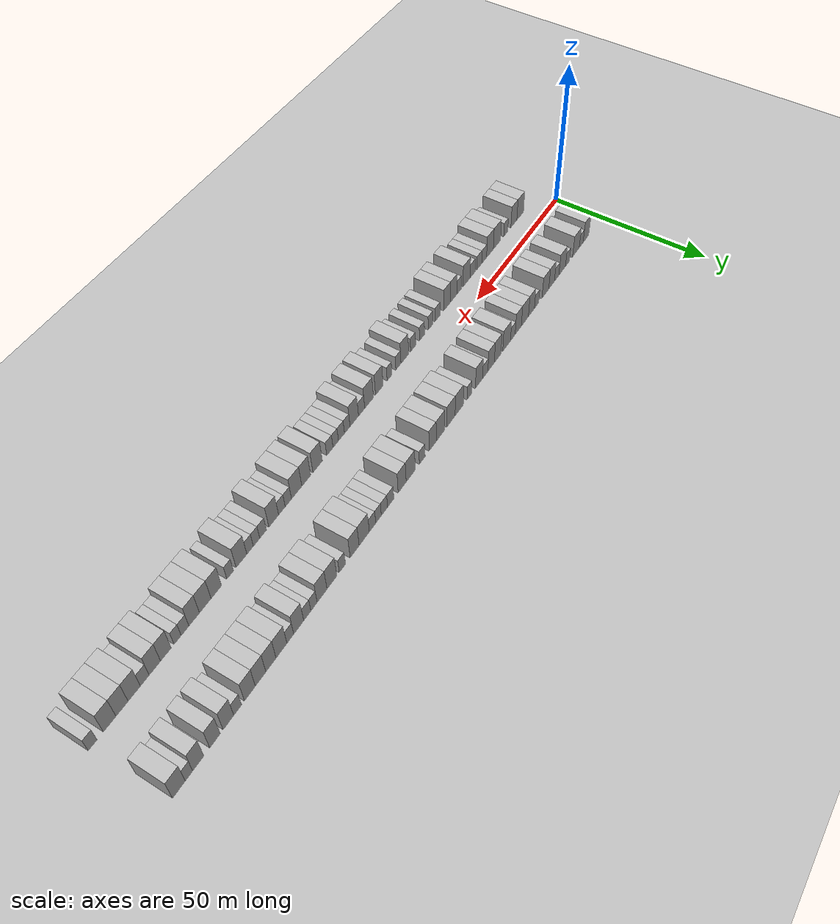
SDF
<?xml version="1.0" encoding="utf-8"?>

<sdf version="1.6">

   <world name="default">

      <gui fullscreen="0">

         <camera name="user_camera">

            <pose>-15 0 4.57585 0 0 0</pose>

            <view_controller>orbit</view_controller>

         </camera>

      </gui>

      <scene>

         <sky>

           <clouds>

             <speed>12</speed>

           </clouds>

         </sky>

         <ambient>0.4 0.4 0.4 1</ambient>

         <background>0.7 0.7 0.7 1</background>

         <shadows>1</shadows>

      </scene>

      <gravity>0 0 -9.8066</gravity>

      <magnetic_field>6e-06 2.3e-05 -4.2e-05</magnetic_field>

      <physics default="0" name="default_physics" type="ode">

         <ode>

            <solver>

               <type>quick</type>

               <iters>10</iters>

               <sor>1.0</sor>

               <use_dynamic_moi_rescaling>0</use_dynamic_moi_rescaling>

            </solver>

            <constraints>

               <cfm>0</cfm>

               <erp>0.2</erp>

               <contact_max_correcting_vel>100</contact_max_correcting_vel>

               <contact_surface_layer>0.001</contact_surface_layer>

            </constraints>

         </ode>

         <max_step_size>0.004</max_step_size>

         <real_time_factor>1</real_time_factor>

         <real_time_update_rate>250</real_time_update_rate>

      </physics>

      <light name="sun" type="directional">

         <cast_shadows>1</cast_shadows>

         <pose>0 0 10 0 0 0</pose>

         <diffuse>0.8 0.8 0.8 1</diffuse>

         <specular>0.2 0.2 0.2 1</specular>

         <attenuation>

            <range>1000</range>

            <constant>0.9</constant>

            <linear>0.01</linear>

            <quadratic>0.001</quadratic>

         </attenuation>

         <direction>-0.5 0.1 -0.9</direction>

      </light>

      <include>

         <name>ground_plane_1</name>

         <uri>model://HANNAS_ground_plane</uri>

         <pose>0 0 0  0 0 0</pose>

      </include>

      <include>

         <name>ground_plane_2</name>

         <uri>model://HANNAS_ground_plane</uri>

         <pose>100 0 0  0 0 0</pose>

      </include>

      <model name="building_1">

         <static>1</static>

         <pose frame="">11.9431 11.0000 0 0.000000 0.000000 1.570796</pose>

         <link name="link">

            <pose frame="">0 0 4.50 0 0 0</pose>

            <collision name="collision">

               <geometry>

                  <box>

                     <size>10.0000 3.8863 9.0000</size>

                  </box>

               </geometry>

               <max_contacts>10</max_contacts>

               <surface>

                  <contact>

                     <ode/>

                  </contact>

                  <bounce/>

                  <friction>

                     <torsional>

                        <ode/>

                     </torsional>

                     <ode/>

                  </friction>

               </surface>

            </collision>

            <visual name="visual">

               <cast_shadows>0</cast_shadows>

               <geometry>

                  <box>

                     <size>10.0000 3.8863 9.0000</size>

                  </box>

               </geometry>

               <material>

                  <script>

                     <uri>model://HANNAS_wall/materials/scripts</uri>

                     <uri>model://HANNAS_wall/materials/textures</uri>

                     <name>vrc/HANNAS_wall</name>

                  </script>

               </material>

            </visual>

            <self_collide>0</self_collide>

            <enable_wind>0</enable_wind>

            <kinematic>0</kinematic>

         </link>

      </model>

      <model name="building_2">

         <static>1</static>

         <pose frame="">15.1962 11.0000 0 0.000000 0.000000 1.570796</pose>

         <link name="link">

            <pose frame="">0 0 3.00 0 0 0</pose>

            <collision name="collision">

               <geometry>

                  <box>

                     <size>10.0000 2.6198 6.0000</size>

                  </box>

               </geometry>

               <max_contacts>10</max_contacts>

               <surface>

                  <contact>

                     <ode/>

                  </contact>

                  <bounce/>

                  <friction>

                     <torsional>

                        <ode/>

                     </torsional>

                     <ode/>

                  </friction>

               </surface>

            </collision>

            <visual name="visual">

               <cast_shadows>0</cast_shadows>

               <geometry>

                  <box>

                     <size>10.0000 2.6198 6.0000</size>

                  </box>

               </geometry>

               <material>

                  <script>

                     <uri>model://HANNAS_wall/materials/scripts</uri>

                     <uri>model://HANNAS_wall/materials/textures</uri>

                     <name>vrc/HANNAS_wall</name>

                  </script>

               </material>

            </visual>

            <self_collide>0</self_collide>

            <enable_wind>0</enable_wind>

            <kinematic>0</kinematic>

         </link>

      </model>

      <model name="building_3">

         <static>1</static>

         <pose frame="">18.7372 11.0000 0 0.000000 0.000000 1.570796</pose>

         <link name="link">

            <pose frame="">0 0 4.50 0 0 0</pose>

            <collision name="collision">

               <geometry>

                  <box>

                     <size>10.0000 4.4623 9.0000</size>

                  </box>

               </geometry>

               <max_contacts>10</max_contacts>

               <surface>

                  <contact>

                     <ode/>

                  </contact>

                  <bounce/>

                  <friction>

                     <torsional>

                        <ode/>

                     </torsional>

                     <ode/>

                  </friction>

               </surface>

            </collision>

            <visual name="visual">

               <cast_shadows>0</cast_shadows>

               <geometry>

                  <box>

                     <size>10.0000 4.4623 9.0000</size>

                  </box>

               </geometry>

               <material>

                  <script>

                     <uri>model://HANNAS_wall/materials/scripts</uri>

                     <uri>model://HANNAS_wall/materials/textures</uri>

                     <name>vrc/HANNAS_wall</name>

                  </script>

               </material>

            </visual>

            <self_collide>0</self_collide>

            <enable_wind>0</enable_wind>

            <kinematic>0</kinematic>

         </link>

      </model>

      <model name="building_4">

         <static>1</static>

         <pose frame="">24.3067 11.0000 0 0.000000 0.000000 1.570796</pose>

         <link name="link">

            <pose frame="">0 0 3.00 0 0 0</pose>

            <collision name="collision">

               <geometry>

                  <box>

                     <size>10.0000 2.6766 6.0000</size>

                  </box>

               </geometry>

               <max_contacts>10</max_contacts>

               <surface>

                  <contact>

                     <ode/>

                  </contact>

                  <bounce/>

                  <friction>

                     <torsional>

                        <ode/>

                     </torsional>

                     <ode/>

                  </friction>

               </surface>

            </collision>

            <visual name="visual">

               <cast_shadows>0</cast_shadows>

               <geometry>

                  <box>

                     <size>10.0000 2.6766 6.0000</size>

                  </box>

               </geometry>

               <material>

                  <script>

                     <uri>model://HANNAS_wall/materials/scripts</uri>

                     <uri>model://HANNAS_wall/materials/textures</uri>

                     <name>vrc/HANNAS_wall</name>

                  </script>

               </material>

            </visual>

            <self_collide>0</self_collide>

            <enable_wind>0</enable_wind>

            <kinematic>0</kinematic>

         </link>

      </model>

      <model name="building_5">

         <static>1</static>

         <pose frame="">27.7889 11.0000 0 0.000000 0.000000 1.570796</pose>

         <link name="link">

            <pose frame="">0 0 4.50 0 0 0</pose>

            <collision name="collision">

               <geometry>

                  <box>

                     <size>10.0000 4.2879 9.0000</size>

                  </box>

               </geometry>

               <max_contacts>10</max_contacts>

               <surface>

                  <contact>

                     <ode/>

                  </contact>

                  <bounce/>

                  <friction>

                     <torsional>

                        <ode/>

                     </torsional>

                     <ode/>

                  </friction>

               </surface>

            </collision>

            <visual name="visual">

               <cast_shadows>0</cast_shadows>

               <geometry>

                  <box>

                     <size>10.0000 4.2879 9.0000</size>

                  </box>

               </geometry>

               <material>

                  <script>

                     <uri>model://HANNAS_wall/materials/scripts</uri>

                     <uri>model://HANNAS_wall/materials/textures</uri>

                     <name>vrc/HANNAS_wall</name>

                  </script>

               </material>

            </visual>

            <self_collide>0</self_collide>

            <enable_wind>0</enable_wind>

            <kinematic>0</kinematic>

         </link>

      </model>

      <model name="building_6">

         <static>1</static>

         <pose frame="">31.3491 11.0000 0 0.000000 0.000000 1.570796</pose>

         <link name="link">

            <pose frame="">0 0 3.00 0 0 0</pose>

            <collision name="collision">

               <geometry>

                  <box>

                     <size>10.0000 2.8324 6.0000</size>

                  </box>

               </geometry>

               <max_contacts>10</max_contacts>

               <surface>

                  <contact>

                     <ode/>

                  </contact>

                  <bounce/>

                  <friction>

                     <torsional>

                        <ode/>

                     </torsional>

                     <ode/>

                  </friction>

               </surface>

            </collision>

            <visual name="visual">

               <cast_shadows>0</cast_shadows>

               <geometry>

                  <box>

                     <size>10.0000 2.8324 6.0000</size>

                  </box>

               </geometry>

               <material>

                  <script>

                     <uri>model://HANNAS_wall/materials/scripts</uri>

                     <uri>model://HANNAS_wall/materials/textures</uri>

                     <name>vrc/HANNAS_wall</name>

                  </script>

               </material>

            </visual>

            <self_collide>0</self_collide>

            <enable_wind>0</enable_wind>

            <kinematic>0</kinematic>

         </link>

      </model>

      <model name="building_7">

         <static>1</static>

         <pose frame="">34.5846 11.0000 0 0.000000 0.000000 1.570796</pose>

         <link name="link">

            <pose frame="">0 0 4.50 0 0 0</pose>

            <collision name="collision">

               <geometry>

                  <box>

                     <size>10.0000 3.6387 9.0000</size>

                  </box>

               </geometry>

               <max_contacts>10</max_contacts>

               <surface>

                  <contact>

                     <ode/>

                  </contact>

                  <bounce/>

                  <friction>

                     <torsional>

                        <ode/>

                     </torsional>

                     <ode/>

                  </friction>

               </surface>

            </collision>

            <visual name="visual">

               <cast_shadows>0</cast_shadows>

               <geometry>

                  <box>

                     <size>10.0000 3.6387 9.0000</size>

                  </box>

               </geometry>

               <material>

                  <script>

                     <uri>model://HANNAS_wall/materials/scripts</uri>

                     <uri>model://HANNAS_wall/materials/textures</uri>

                     <name>vrc/HANNAS_wall</name>

                  </script>

               </material>

            </visual>

            <self_collide>0</self_collide>

            <enable_wind>0</enable_wind>

            <kinematic>0</kinematic>

         </link>

      </model>

      <model name="building_8">

         <static>1</static>

         <pose frame="">38.5252 11.0000 0 0.000000 0.000000 1.570796</pose>

         <link name="link">

            <pose frame="">0 0 4.50 0 0 0</pose>

            <collision name="collision">

               <geometry>

                  <box>

                     <size>10.0000 4.2426 9.0000</size>

                  </box>

               </geometry>

               <max_contacts>10</max_contacts>

               <surface>

                  <contact>

                     <ode/>

                  </contact>

                  <bounce/>

                  <friction>

                     <torsional>

                        <ode/>

                     </torsional>

                     <ode/>

                  </friction>

               </surface>

            </collision>

            <visual name="visual">

               <cast_shadows>0</cast_shadows>

               <geometry>

                  <box>

                     <size>10.0000 4.2426 9.0000</size>

                  </box>

               </geometry>

               <material>

                  <script>

                     <uri>model://HANNAS_wall/materials/scripts</uri>

                     <uri>model://HANNAS_wall/materials/textures</uri>

                     <name>vrc/HANNAS_wall</name>

                  </script>

               </material>

            </visual>

            <self_collide>0</self_collide>

            <enable_wind>0</enable_wind>

            <kinematic>0</kinematic>

         </link>

      </model>

      <model name="building_9">

         <static>1</static>

         <pose frame="">43.9767 11.0000 0 0.000000 0.000000 1.570796</pose>

         <link name="link">

            <pose frame="">0 0 3.00 0 0 0</pose>

            <collision name="collision">

               <geometry>

                  <box>

                     <size>10.0000 2.6604 6.0000</size>

                  </box>

               </geometry>

               <max_contacts>10</max_contacts>

               <surface>

                  <contact>

                     <ode/>

                  </contact>

                  <bounce/>

                  <friction>

                     <torsional>

                        <ode/>

                     </torsional>

                     <ode/>

                  </friction>

               </surface>

            </collision>

            <visual name="visual">

               <cast_shadows>0</cast_shadows>

               <geometry>

                  <box>

                     <size>10.0000 2.6604 6.0000</size>

                  </box>

               </geometry>

               <material>

                  <script>

                     <uri>model://HANNAS_wall/materials/scripts</uri>

                     <uri>model://HANNAS_wall/materials/textures</uri>

                     <name>vrc/HANNAS_wall</name>

                  </script>

               </material>

            </visual>

            <self_collide>0</self_collide>

            <enable_wind>0</enable_wind>

            <kinematic>0</kinematic>

         </link>

      </model>

      <model name="building_10">

         <static>1</static>

         <pose frame="">47.1235 11.0000 0 0.000000 0.000000 1.570796</pose>

         <link name="link">

            <pose frame="">0 0 4.50 0 0 0</pose>

            <collision name="collision">

               <geometry>

                  <box>

                     <size>10.0000 3.6331 9.0000</size>

                  </box>

               </geometry>

               <max_contacts>10</max_contacts>

               <surface>

                  <contact>

                     <ode/>

                  </contact>

                  <bounce/>

                  <friction>

                     <torsional>

                        <ode/>

                     </torsional>

                     <ode/>

                  </friction>

               </surface>

            </collision>

            <visual name="visual">

               <cast_shadows>0</cast_shadows>

               <geometry>

                  <box>

                     <size>10.0000 3.6331 9.0000</size>

                  </box>

               </geometry>

               <material>

                  <script>

                     <uri>model://HANNAS_wall/materials/scripts</uri>

                     <uri>model://HANNAS_wall/materials/textures</uri>

                     <name>vrc/HANNAS_wall</name>

                  </script>

               </material>

            </visual>

            <self_collide>0</self_collide>

            <enable_wind>0</enable_wind>

            <kinematic>0</kinematic>

         </link>

      </model>

      <model name="building_11">

         <static>1</static>

         <pose frame="">51.0800 11.0000 0 0.000000 0.000000 1.570796</pose>

         <link name="link">

            <pose frame="">0 0 4.50 0 0 0</pose>

            <collision name="collision">

               <geometry>

                  <box>

                     <size>10.0000 4.2798 9.0000</size>

                  </box>

               </geometry>

               <max_contacts>10</max_contacts>

               <surface>

                  <contact>

                     <ode/>

                  </contact>

                  <bounce/>

                  <friction>

                     <torsional>

                        <ode/>

                     </torsional>

                     <ode/>

                  </friction>

               </surface>

            </collision>

            <visual name="visual">

               <cast_shadows>0</cast_shadows>

               <geometry>

                  <box>

                     <size>10.0000 4.2798 9.0000</size>

                  </box>

               </geometry>

               <material>

                  <script>

                     <uri>model://HANNAS_wall/materials/scripts</uri>

                     <uri>model://HANNAS_wall/materials/textures</uri>

                     <name>vrc/HANNAS_wall</name>

                  </script>

               </material>

            </visual>

            <self_collide>0</self_collide>

            <enable_wind>0</enable_wind>

            <kinematic>0</kinematic>

         </link>

      </model>

      <model name="building_12">

         <static>1</static>

         <pose frame="">55.0376 11.0000 0 0.000000 0.000000 1.570796</pose>

         <link name="link">

            <pose frame="">0 0 4.50 0 0 0</pose>

            <collision name="collision">

               <geometry>

                  <box>

                     <size>10.0000 3.6354 9.0000</size>

                  </box>

               </geometry>

               <max_contacts>10</max_contacts>

               <surface>

                  <contact>

                     <ode/>

                  </contact>

                  <bounce/>

                  <friction>

                     <torsional>

                        <ode/>

                     </torsional>

                     <ode/>

                  </friction>

               </surface>

            </collision>

            <visual name="visual">

               <cast_shadows>0</cast_shadows>

               <geometry>

                  <box>

                     <size>10.0000 3.6354 9.0000</size>

                  </box>

               </geometry>

               <material>

                  <script>

                     <uri>model://HANNAS_wall/materials/scripts</uri>

                     <uri>model://HANNAS_wall/materials/textures</uri>

                     <name>vrc/HANNAS_wall</name>

                  </script>

               </material>

            </visual>

            <self_collide>0</self_collide>

            <enable_wind>0</enable_wind>

            <kinematic>0</kinematic>

         </link>

      </model>

      <model name="building_13">

         <static>1</static>

         <pose frame="">58.2341 11.0000 0 0.000000 0.000000 1.570796</pose>

         <link name="link">

            <pose frame="">0 0 3.00 0 0 0</pose>

            <collision name="collision">

               <geometry>

                  <box>

                     <size>10.0000 2.7576 6.0000</size>

                  </box>

               </geometry>

               <max_contacts>10</max_contacts>

               <surface>

                  <contact>

                     <ode/>

                  </contact>

                  <bounce/>

                  <friction>

                     <torsional>

                        <ode/>

                     </torsional>

                     <ode/>

                  </friction>

               </surface>

            </collision>

            <visual name="visual">

               <cast_shadows>0</cast_shadows>

               <geometry>

                  <box>

                     <size>10.0000 2.7576 6.0000</size>

                  </box>

               </geometry>

               <material>

                  <script>

                     <uri>model://HANNAS_wall/materials/scripts</uri>

                     <uri>model://HANNAS_wall/materials/textures</uri>

                     <name>vrc/HANNAS_wall</name>

                  </script>

               </material>

            </visual>

            <self_collide>0</self_collide>

            <enable_wind>0</enable_wind>

            <kinematic>0</kinematic>

         </link>

      </model>

      <model name="building_14">

         <static>1</static>

         <pose frame="">61.8571 11.0000 0 0.000000 0.000000 1.570796</pose>

         <link name="link">

            <pose frame="">0 0 4.50 0 0 0</pose>

            <collision name="collision">

               <geometry>

                  <box>

                     <size>10.0000 4.4884 9.0000</size>

                  </box>

               </geometry>

               <max_contacts>10</max_contacts>

               <surface>

                  <contact>

                     <ode/>

                  </contact>

                  <bounce/>

                  <friction>

                     <torsional>

                        <ode/>

                     </torsional>

                     <ode/>

                  </friction>

               </surface>

            </collision>

            <visual name="visual">

               <cast_shadows>0</cast_shadows>

               <geometry>

                  <box>

                     <size>10.0000 4.4884 9.0000</size>

                  </box>

               </geometry>

               <material>

                  <script>

                     <uri>model://HANNAS_wall/materials/scripts</uri>

                     <uri>model://HANNAS_wall/materials/textures</uri>

                     <name>vrc/HANNAS_wall</name>

                  </script>

               </material>

            </visual>

            <self_collide>0</self_collide>

            <enable_wind>0</enable_wind>

            <kinematic>0</kinematic>

         </link>

      </model>

      <model name="building_15">

         <static>1</static>

         <pose frame="">66.9812 11.0000 0 0.000000 0.000000 1.570796</pose>

         <link name="link">

            <pose frame="">0 0 4.50 0 0 0</pose>

            <collision name="collision">

               <geometry>

                  <box>

                     <size>10.0000 3.7596 9.0000</size>

                  </box>

               </geometry>

               <max_contacts>10</max_contacts>

               <surface>

                  <contact>

                     <ode/>

                  </contact>

                  <bounce/>

                  <friction>

                     <torsional>

                        <ode/>

                     </torsional>

                     <ode/>

                  </friction>

               </surface>

            </collision>

            <visual name="visual">

               <cast_shadows>0</cast_shadows>

               <geometry>

                  <box>

                     <size>10.0000 3.7596 9.0000</size>

                  </box>

               </geometry>

               <material>

                  <script>

                     <uri>model://HANNAS_wall/materials/scripts</uri>

                     <uri>model://HANNAS_wall/materials/textures</uri>

                     <name>vrc/HANNAS_wall</name>

                  </script>

               </material>

            </visual>

            <self_collide>0</self_collide>

            <enable_wind>0</enable_wind>

            <kinematic>0</kinematic>

         </link>

      </model>

      <model name="building_16">

         <static>1</static>

         <pose frame="">70.6647 11.0000 0 0.000000 0.000000 1.570796</pose>

         <link name="link">

            <pose frame="">0 0 4.50 0 0 0</pose>

            <collision name="collision">

               <geometry>

                  <box>

                     <size>10.0000 3.6075 9.0000</size>

                  </box>

               </geometry>

               <max_contacts>10</max_contacts>

               <surface>

                  <contact>

                     <ode/>

                  </contact>

                  <bounce/>

                  <friction>

                     <torsional>

                        <ode/>

                     </torsional>

                     <ode/>

                  </friction>

               </surface>

            </collision>

            <visual name="visual">

               <cast_shadows>0</cast_shadows>

               <geometry>

                  <box>

                     <size>10.0000 3.6075 9.0000</size>

                  </box>

               </geometry>

               <material>

                  <script>

                     <uri>model://HANNAS_wall/materials/scripts</uri>

                     <uri>model://HANNAS_wall/materials/textures</uri>

                     <name>vrc/HANNAS_wall</name>

                  </script>

               </material>

            </visual>

            <self_collide>0</self_collide>

            <enable_wind>0</enable_wind>

            <kinematic>0</kinematic>

         </link>

      </model>

      <model name="building_17">

         <static>1</static>

         <pose frame="">73.9417 11.0000 0 0.000000 0.000000 1.570796</pose>

         <link name="link">

            <pose frame="">0 0 3.00 0 0 0</pose>

            <collision name="collision">

               <geometry>

                  <box>

                     <size>10.0000 2.9465 6.0000</size>

                  </box>

               </geometry>

               <max_contacts>10</max_contacts>

               <surface>

                  <contact>

                     <ode/>

                  </contact>

                  <bounce/>

                  <friction>

                     <torsional>

                        <ode/>

                     </torsional>

                     <ode/>

                  </friction>

               </surface>

            </collision>

            <visual name="visual">

               <cast_shadows>0</cast_shadows>

               <geometry>

                  <box>

                     <size>10.0000 2.9465 6.0000</size>

                  </box>

               </geometry>

               <material>

                  <script>

                     <uri>model://HANNAS_wall/materials/scripts</uri>

                     <uri>model://HANNAS_wall/materials/textures</uri>

                     <name>vrc/HANNAS_wall</name>

                  </script>

               </material>

            </visual>

            <self_collide>0</self_collide>

            <enable_wind>0</enable_wind>

            <kinematic>0</kinematic>

         </link>

      </model>

      <model name="building_18">

         <static>1</static>

         <pose frame="">77.3780 11.0000 0 0.000000 0.000000 1.570796</pose>

         <link name="link">

            <pose frame="">0 0 4.50 0 0 0</pose>

            <collision name="collision">

               <geometry>

                  <box>

                     <size>10.0000 3.9261 9.0000</size>

                  </box>

               </geometry>

               <max_contacts>10</max_contacts>

               <surface>

                  <contact>

                     <ode/>

                  </contact>

                  <bounce/>

                  <friction>

                     <torsional>

                        <ode/>

                     </torsional>

                     <ode/>

                  </friction>

               </surface>

            </collision>

            <visual name="visual">

               <cast_shadows>0</cast_shadows>

               <geometry>

                  <box>

                     <size>10.0000 3.9261 9.0000</size>

                  </box>

               </geometry>

               <material>

                  <script>

                     <uri>model://HANNAS_wall/materials/scripts</uri>

                     <uri>model://HANNAS_wall/materials/textures</uri>

                     <name>vrc/HANNAS_wall</name>

                  </script>

               </material>

            </visual>

            <self_collide>0</self_collide>

            <enable_wind>0</enable_wind>

            <kinematic>0</kinematic>

         </link>

      </model>

      <model name="building_19">

         <static>1</static>

         <pose frame="">82.6118 11.0000 0 0.000000 0.000000 1.570796</pose>

         <link name="link">

            <pose frame="">0 0 3.00 0 0 0</pose>

            <collision name="collision">

               <geometry>

                  <box>

                     <size>10.0000 2.5414 6.0000</size>

                  </box>

               </geometry>

               <max_contacts>10</max_contacts>

               <surface>

                  <contact>

                     <ode/>

                  </contact>

                  <bounce/>

                  <friction>

                     <torsional>

                        <ode/>

                     </torsional>

                     <ode/>

                  </friction>

               </surface>

            </collision>

            <visual name="visual">

               <cast_shadows>0</cast_shadows>

               <geometry>

                  <box>

                     <size>10.0000 2.5414 6.0000</size>

                  </box>

               </geometry>

               <material>

                  <script>

                     <uri>model://HANNAS_wall/materials/scripts</uri>

                     <uri>model://HANNAS_wall/materials/textures</uri>

                     <name>vrc/HANNAS_wall</name>

                  </script>

               </material>

            </visual>

            <self_collide>0</self_collide>

            <enable_wind>0</enable_wind>

            <kinematic>0</kinematic>

         </link>

      </model>

      <model name="building_20">

         <static>1</static>

         <pose frame="">88.0223 11.0000 0 0.000000 0.000000 1.570796</pose>

         <link name="link">

            <pose frame="">0 0 4.50 0 0 0</pose>

            <collision name="collision">

               <geometry>

                  <box>

                     <size>10.0000 4.2796 9.0000</size>

                  </box>

               </geometry>

               <max_contacts>10</max_contacts>

               <surface>

                  <contact>

                     <ode/>

                  </contact>

                  <bounce/>

                  <friction>

                     <torsional>

                        <ode/>

                     </torsional>

                     <ode/>

                  </friction>

               </surface>

            </collision>

            <visual name="visual">

               <cast_shadows>0</cast_shadows>

               <geometry>

                  <box>

                     <size>10.0000 4.2796 9.0000</size>

                  </box>

               </geometry>

               <material>

                  <script>

                     <uri>model://HANNAS_wall/materials/scripts</uri>

                     <uri>model://HANNAS_wall/materials/textures</uri>

                     <name>vrc/HANNAS_wall</name>

                  </script>

               </material>

            </visual>

            <self_collide>0</self_collide>

            <enable_wind>0</enable_wind>

            <kinematic>0</kinematic>

         </link>

      </model>

      <model name="building_21">

         <static>1</static>

         <pose frame="">92.3208 11.0000 0 0.000000 0.000000 1.570796</pose>

         <link name="link">

            <pose frame="">0 0 4.50 0 0 0</pose>

            <collision name="collision">

               <geometry>

                  <box>

                     <size>10.0000 4.3175 9.0000</size>

                  </box>

               </geometry>

               <max_contacts>10</max_contacts>

               <surface>

                  <contact>

                     <ode/>

                  </contact>

                  <bounce/>

                  <friction>

                     <torsional>

                        <ode/>

                     </torsional>

                     <ode/>

                  </friction>

               </surface>

            </collision>

            <visual name="visual">

               <cast_shadows>0</cast_shadows>

               <geometry>

                  <box>

                     <size>10.0000 4.3175 9.0000</size>

                  </box>

               </geometry>

               <material>

                  <script>

                     <uri>model://HANNAS_wall/materials/scripts</uri>

                     <uri>model://HANNAS_wall/materials/textures</uri>

                     <name>vrc/HANNAS_wall</name>

                  </script>

               </material>

            </visual>

            <self_collide>0</self_collide>

            <enable_wind>0</enable_wind>

            <kinematic>0</kinematic>

         </link>

      </model>

      <model name="building_22">

         <static>1</static>

         <pose frame="">97.6514 11.0000 0 0.000000 0.000000 1.570796</pose>

         <link name="link">

            <pose frame="">0 0 4.50 0 0 0</pose>

            <collision name="collision">

               <geometry>

                  <box>

                     <size>10.0000 4.3437 9.0000</size>

                  </box>

               </geometry>

               <max_contacts>10</max_contacts>

               <surface>

                  <contact>

                     <ode/>

                  </contact>

                  <bounce/>

                  <friction>

                     <torsional>

                        <ode/>

                     </torsional>

                     <ode/>

                  </friction>

               </surface>

            </collision>

            <visual name="visual">

               <cast_shadows>0</cast_shadows>

               <geometry>

                  <box>

                     <size>10.0000 4.3437 9.0000</size>

                  </box>

               </geometry>

               <material>

                  <script>

                     <uri>model://HANNAS_wall/materials/scripts</uri>

                     <uri>model://HANNAS_wall/materials/textures</uri>

                     <name>vrc/HANNAS_wall</name>

                  </script>

               </material>

            </visual>

            <self_collide>0</self_collide>

            <enable_wind>0</enable_wind>

            <kinematic>0</kinematic>

         </link>

      </model>

      <model name="building_23">

         <static>1</static>

         <pose frame="">101.6237 11.0000 0 0.000000 0.000000 1.570796</pose>

         <link name="link">

            <pose frame="">0 0 4.50 0 0 0</pose>

            <collision name="collision">

               <geometry>

                  <box>

                     <size>10.0000 3.6009 9.0000</size>

                  </box>

               </geometry>

               <max_contacts>10</max_contacts>

               <surface>

                  <contact>

                     <ode/>

                  </contact>

                  <bounce/>

                  <friction>

                     <torsional>

                        <ode/>

                     </torsional>

                     <ode/>

                  </friction>

               </surface>

            </collision>

            <visual name="visual">

               <cast_shadows>0</cast_shadows>

               <geometry>

                  <box>

                     <size>10.0000 3.6009 9.0000</size>

                  </box>

               </geometry>

               <material>

                  <script>

                     <uri>model://HANNAS_wall/materials/scripts</uri>

                     <uri>model://HANNAS_wall/materials/textures</uri>

                     <name>vrc/HANNAS_wall</name>

                  </script>

               </material>

            </visual>

            <self_collide>0</self_collide>

            <enable_wind>0</enable_wind>

            <kinematic>0</kinematic>

         </link>

      </model>

      <model name="building_24">

         <static>1</static>

         <pose frame="">106.8404 11.0000 0 0.000000 0.000000 1.570796</pose>

         <link name="link">

            <pose frame="">0 0 3.00 0 0 0</pose>

            <collision name="collision">

               <geometry>

                  <box>

                     <size>10.0000 2.8325 6.0000</size>

                  </box>

               </geometry>

               <max_contacts>10</max_contacts>

               <surface>

                  <contact>

                     <ode/>

                  </contact>

                  <bounce/>

                  <friction>

                     <torsional>

                        <ode/>

                     </torsional>

                     <ode/>

                  </friction>

               </surface>

            </collision>

            <visual name="visual">

               <cast_shadows>0</cast_shadows>

               <geometry>

                  <box>

                     <size>10.0000 2.8325 6.0000</size>

                  </box>

               </geometry>

               <material>

                  <script>

                     <uri>model://HANNAS_wall/materials/scripts</uri>

                     <uri>model://HANNAS_wall/materials/textures</uri>

                     <name>vrc/HANNAS_wall</name>

                  </script>

               </material>

            </visual>

            <self_collide>0</self_collide>

            <enable_wind>0</enable_wind>

            <kinematic>0</kinematic>

         </link>

      </model>

      <model name="building_25">

         <static>1</static>

         <pose frame="">112.4384 11.0000 0 0.000000 0.000000 1.570796</pose>

         <link name="link">

            <pose frame="">0 0 4.50 0 0 0</pose>

            <collision name="collision">

               <geometry>

                  <box>

                     <size>10.0000 4.3634 9.0000</size>

                  </box>

               </geometry>

               <max_contacts>10</max_contacts>

               <surface>

                  <contact>

                     <ode/>

                  </contact>

                  <bounce/>

                  <friction>

                     <torsional>

                        <ode/>

                     </torsional>

                     <ode/>

                  </friction>

               </surface>

            </collision>

            <visual name="visual">

               <cast_shadows>0</cast_shadows>

               <geometry>

                  <box>

                     <size>10.0000 4.3634 9.0000</size>

                  </box>

               </geometry>

               <material>

                  <script>

                     <uri>model://HANNAS_wall/materials/scripts</uri>

                     <uri>model://HANNAS_wall/materials/textures</uri>

                     <name>vrc/HANNAS_wall</name>

                  </script>

               </material>

            </visual>

            <self_collide>0</self_collide>

            <enable_wind>0</enable_wind>

            <kinematic>0</kinematic>

         </link>

      </model>

      <model name="building_26">

         <static>1</static>

         <pose frame="">116.5243 11.0000 0 0.000000 0.000000 1.570796</pose>

         <link name="link">

            <pose frame="">0 0 4.50 0 0 0</pose>

            <collision name="collision">

               <geometry>

                  <box>

                     <size>10.0000 3.8084 9.0000</size>

                  </box>

               </geometry>

               <max_contacts>10</max_contacts>

               <surface>

                  <contact>

                     <ode/>

                  </contact>

                  <bounce/>

                  <friction>

                     <torsional>

                        <ode/>

                     </torsional>

                     <ode/>

                  </friction>

               </surface>

            </collision>

            <visual name="visual">

               <cast_shadows>0</cast_shadows>

               <geometry>

                  <box>

                     <size>10.0000 3.8084 9.0000</size>

                  </box>

               </geometry>

               <material>

                  <script>

                     <uri>model://HANNAS_wall/materials/scripts</uri>

                     <uri>model://HANNAS_wall/materials/textures</uri>

                     <name>vrc/HANNAS_wall</name>

                  </script>

               </material>

            </visual>

            <self_collide>0</self_collide>

            <enable_wind>0</enable_wind>

            <kinematic>0</kinematic>

         </link>

      </model>

      <model name="building_27">

         <static>1</static>

         <pose frame="">121.8879 11.0000 0 0.000000 0.000000 1.570796</pose>

         <link name="link">

            <pose frame="">0 0 3.00 0 0 0</pose>

            <collision name="collision">

               <geometry>

                  <box>

                     <size>10.0000 2.9187 6.0000</size>

                  </box>

               </geometry>

               <max_contacts>10</max_contacts>

               <surface>

                  <contact>

                     <ode/>

                  </contact>

                  <bounce/>

                  <friction>

                     <torsional>

                        <ode/>

                     </torsional>

                     <ode/>

                  </friction>

               </surface>

            </collision>

            <visual name="visual">

               <cast_shadows>0</cast_shadows>

               <geometry>

                  <box>

                     <size>10.0000 2.9187 6.0000</size>

                  </box>

               </geometry>

               <material>

                  <script>

                     <uri>model://HANNAS_wall/materials/scripts</uri>

                     <uri>model://HANNAS_wall/materials/textures</uri>

                     <name>vrc/HANNAS_wall</name>

                  </script>

               </material>

            </visual>

            <self_collide>0</self_collide>

            <enable_wind>0</enable_wind>

            <kinematic>0</kinematic>

         </link>

      </model>

      <model name="building_28">

         <static>1</static>

         <pose frame="">124.7764 11.0000 0 0.000000 0.000000 1.570796</pose>

         <link name="link">

            <pose frame="">0 0 3.00 0 0 0</pose>

            <collision name="collision">

               <geometry>

                  <box>

                     <size>10.0000 2.8584 6.0000</size>

                  </box>

               </geometry>

               <max_contacts>10</max_contacts>

               <surface>

                  <contact>

                     <ode/>

                  </contact>

                  <bounce/>

                  <friction>

                     <torsional>

                        <ode/>

                     </torsional>

                     <ode/>

                  </friction>

               </surface>

            </collision>

            <visual name="visual">

               <cast_shadows>0</cast_shadows>

               <geometry>

                  <box>

                     <size>10.0000 2.8584 6.0000</size>

                  </box>

               </geometry>

               <material>

                  <script>

                     <uri>model://HANNAS_wall/materials/scripts</uri>

                     <uri>model://HANNAS_wall/materials/textures</uri>

                     <name>vrc/HANNAS_wall</name>

                  </script>

               </material>

            </visual>

            <self_collide>0</self_collide>

            <enable_wind>0</enable_wind>

            <kinematic>0</kinematic>

         </link>

      </model>

      <model name="building_29">

         <static>1</static>

         <pose frame="">127.4666 11.0000 0 0.000000 0.000000 1.570796</pose>

         <link name="link">

            <pose frame="">0 0 3.00 0 0 0</pose>

            <collision name="collision">

               <geometry>

                  <box>

                     <size>10.0000 2.5221 6.0000</size>

                  </box>

               </geometry>

               <max_contacts>10</max_contacts>

               <surface>

                  <contact>

                     <ode/>

                  </contact>

                  <bounce/>

                  <friction>

                     <torsional>

                        <ode/>

                     </torsional>

                     <ode/>

                  </friction>

               </surface>

            </collision>

            <visual name="visual">

               <cast_shadows>0</cast_shadows>

               <geometry>

                  <box>

                     <size>10.0000 2.5221 6.0000</size>

                  </box>

               </geometry>

               <material>

                  <script>

                     <uri>model://HANNAS_wall/materials/scripts</uri>

                     <uri>model://HANNAS_wall/materials/textures</uri>

                     <name>vrc/HANNAS_wall</name>

                  </script>

               </material>

            </visual>

            <self_collide>0</self_collide>

            <enable_wind>0</enable_wind>

            <kinematic>0</kinematic>

         </link>

      </model>

      <model name="building_30">

         <static>1</static>

         <pose frame="">130.1689 11.0000 0 0.000000 0.000000 1.570796</pose>

         <link name="link">

            <pose frame="">0 0 3.00 0 0 0</pose>

            <collision name="collision">

               <geometry>

                  <box>

                     <size>10.0000 2.8825 6.0000</size>

                  </box>

               </geometry>

               <max_contacts>10</max_contacts>

               <surface>

                  <contact>

                     <ode/>

                  </contact>

                  <bounce/>

                  <friction>

                     <torsional>

                        <ode/>

                     </torsional>

                     <ode/>

                  </friction>

               </surface>

            </collision>

            <visual name="visual">

               <cast_shadows>0</cast_shadows>

               <geometry>

                  <box>

                     <size>10.0000 2.8825 6.0000</size>

                  </box>

               </geometry>

               <material>

                  <script>

                     <uri>model://HANNAS_wall/materials/scripts</uri>

                     <uri>model://HANNAS_wall/materials/textures</uri>

                     <name>vrc/HANNAS_wall</name>

                  </script>

               </material>

            </visual>

            <self_collide>0</self_collide>

            <enable_wind>0</enable_wind>

            <kinematic>0</kinematic>

         </link>

      </model>

      <model name="building_31">

         <static>1</static>

         <pose frame="">133.8577 11.0000 0 0.000000 0.000000 1.570796</pose>

         <link name="link">

            <pose frame="">0 0 4.50 0 0 0</pose>

            <collision name="collision">

               <geometry>

                  <box>

                     <size>10.0000 4.4951 9.0000</size>

                  </box>

               </geometry>

               <max_contacts>10</max_contacts>

               <surface>

                  <contact>

                     <ode/>

                  </contact>

                  <bounce/>

                  <friction>

                     <torsional>

                        <ode/>

                     </torsional>

                     <ode/>

                  </friction>

               </surface>

            </collision>

            <visual name="visual">

               <cast_shadows>0</cast_shadows>

               <geometry>

                  <box>

                     <size>10.0000 4.4951 9.0000</size>

                  </box>

               </geometry>

               <material>

                  <script>

                     <uri>model://HANNAS_wall/materials/scripts</uri>

                     <uri>model://HANNAS_wall/materials/textures</uri>

                     <name>vrc/HANNAS_wall</name>

                  </script>

               </material>

            </visual>

            <self_collide>0</self_collide>

            <enable_wind>0</enable_wind>

            <kinematic>0</kinematic>

         </link>

      </model>

      <model name="building_32">

         <static>1</static>

         <pose frame="">138.0443 11.0000 0 0.000000 0.000000 1.570796</pose>

         <link name="link">

            <pose frame="">0 0 4.50 0 0 0</pose>

            <collision name="collision">

               <geometry>

                  <box>

                     <size>10.0000 3.8781 9.0000</size>

                  </box>

               </geometry>

               <max_contacts>10</max_contacts>

               <surface>

                  <contact>

                     <ode/>

                  </contact>

                  <bounce/>

                  <friction>

                     <torsional>

                        <ode/>

                     </torsional>

                     <ode/>

                  </friction>

               </surface>

            </collision>

            <visual name="visual">

               <cast_shadows>0</cast_shadows>

               <geometry>

                  <box>

                     <size>10.0000 3.8781 9.0000</size>

                  </box>

               </geometry>

               <material>

                  <script>

                     <uri>model://HANNAS_wall/materials/scripts</uri>

                     <uri>model://HANNAS_wall/materials/textures</uri>

                     <name>vrc/HANNAS_wall</name>

                  </script>

               </material>

            </visual>

            <self_collide>0</self_collide>

            <enable_wind>0</enable_wind>

            <kinematic>0</kinematic>

         </link>

      </model>

      <model name="building_33">

         <static>1</static>

         <pose frame="">143.3178 11.0000 0 0.000000 0.000000 1.570796</pose>

         <link name="link">

            <pose frame="">0 0 3.00 0 0 0</pose>

            <collision name="collision">

               <geometry>

                  <box>

                     <size>10.0000 2.6688 6.0000</size>

                  </box>

               </geometry>

               <max_contacts>10</max_contacts>

               <surface>

                  <contact>

                     <ode/>

                  </contact>

                  <bounce/>

                  <friction>

                     <torsional>

                        <ode/>

                     </torsional>

                     <ode/>

                  </friction>

               </surface>

            </collision>

            <visual name="visual">

               <cast_shadows>0</cast_shadows>

               <geometry>

                  <box>

                     <size>10.0000 2.6688 6.0000</size>

                  </box>

               </geometry>

               <material>

                  <script>

                     <uri>model://HANNAS_wall/materials/scripts</uri>

                     <uri>model://HANNAS_wall/materials/textures</uri>

                     <name>vrc/HANNAS_wall</name>

                  </script>

               </material>

            </visual>

            <self_collide>0</self_collide>

            <enable_wind>0</enable_wind>

            <kinematic>0</kinematic>

         </link>

      </model>

      <model name="building_34">

         <static>1</static>

         <pose frame="">147.7226 11.0000 0 0.000000 0.000000 1.570796</pose>

         <link name="link">

            <pose frame="">0 0 4.50 0 0 0</pose>

            <collision name="collision">

               <geometry>

                  <box>

                     <size>10.0000 4.1409 9.0000</size>

                  </box>

               </geometry>

               <max_contacts>10</max_contacts>

               <surface>

                  <contact>

                     <ode/>

                  </contact>

                  <bounce/>

                  <friction>

                     <torsional>

                        <ode/>

                     </torsional>

                     <ode/>

                  </friction>

               </surface>

            </collision>

            <visual name="visual">

               <cast_shadows>0</cast_shadows>

               <geometry>

                  <box>

                     <size>10.0000 4.1409 9.0000</size>

                  </box>

               </geometry>

               <material>

                  <script>

                     <uri>model://HANNAS_wall/materials/scripts</uri>

                     <uri>model://HANNAS_wall/materials/textures</uri>

                     <name>vrc/HANNAS_wall</name>

                  </script>

               </material>

            </visual>

            <self_collide>0</self_collide>

            <enable_wind>0</enable_wind>

            <kinematic>0</kinematic>

         </link>

      </model>

      <model name="building_35">

         <static>1</static>

         <pose frame="">151.8063 11.0000 0 0.000000 0.000000 1.570796</pose>

         <link name="link">

            <pose frame="">0 0 4.50 0 0 0</pose>

            <collision name="collision">

               <geometry>

                  <box>

                     <size>10.0000 4.0263 9.0000</size>

                  </box>

               </geometry>

               <max_contacts>10</max_contacts>

               <surface>

                  <contact>

                     <ode/>

                  </contact>

                  <bounce/>

                  <friction>

                     <torsional>

                        <ode/>

                     </torsional>

                     <ode/>

                  </friction>

               </surface>

            </collision>

            <visual name="visual">

               <cast_shadows>0</cast_shadows>

               <geometry>

                  <box>

                     <size>10.0000 4.0263 9.0000</size>

                  </box>

               </geometry>

               <material>

                  <script>

                     <uri>model://HANNAS_wall/materials/scripts</uri>

                     <uri>model://HANNAS_wall/materials/textures</uri>

                     <name>vrc/HANNAS_wall</name>

                  </script>

               </material>

            </visual>

            <self_collide>0</self_collide>

            <enable_wind>0</enable_wind>

            <kinematic>0</kinematic>

         </link>

      </model>

      <model name="building_36">

         <static>1</static>

         <pose frame="">155.0954 11.0000 0 0.000000 0.000000 1.570796</pose>

         <link name="link">

            <pose frame="">0 0 3.00 0 0 0</pose>

            <collision name="collision">

               <geometry>

                  <box>

                     <size>10.0000 2.5520 6.0000</size>

                  </box>

               </geometry>

               <max_contacts>10</max_contacts>

               <surface>

                  <contact>

                     <ode/>

                  </contact>

                  <bounce/>

                  <friction>

                     <torsional>

                        <ode/>

                     </torsional>

                     <ode/>

                  </friction>

               </surface>

            </collision>

            <visual name="visual">

               <cast_shadows>0</cast_shadows>

               <geometry>

                  <box>

                     <size>10.0000 2.5520 6.0000</size>

                  </box>

               </geometry>

               <material>

                  <script>

                     <uri>model://HANNAS_wall/materials/scripts</uri>

                     <uri>model://HANNAS_wall/materials/textures</uri>

                     <name>vrc/HANNAS_wall</name>

                  </script>

               </material>

            </visual>

            <self_collide>0</self_collide>

            <enable_wind>0</enable_wind>

            <kinematic>0</kinematic>

         </link>

      </model>

      <model name="building_37">

         <static>1</static>

         <pose frame="">157.8028 11.0000 0 0.000000 0.000000 1.570796</pose>

         <link name="link">

            <pose frame="">0 0 3.00 0 0 0</pose>

            <collision name="collision">

               <geometry>

                  <box>

                     <size>10.0000 2.8628 6.0000</size>

                  </box>

               </geometry>

               <max_contacts>10</max_contacts>

               <surface>

                  <contact>

                     <ode/>

                  </contact>

                  <bounce/>

                  <friction>

                     <torsional>

                        <ode/>

                     </torsional>

                     <ode/>

                  </friction>

               </surface>

            </collision>

            <visual name="visual">

               <cast_shadows>0</cast_shadows>

               <geometry>

                  <box>

                     <size>10.0000 2.8628 6.0000</size>

                  </box>

               </geometry>

               <material>

                  <script>

                     <uri>model://HANNAS_wall/materials/scripts</uri>

                     <uri>model://HANNAS_wall/materials/textures</uri>

                     <name>vrc/HANNAS_wall</name>

                  </script>

               </material>

            </visual>

            <self_collide>0</self_collide>

            <enable_wind>0</enable_wind>

            <kinematic>0</kinematic>

         </link>

      </model>

      <model name="building_38">

         <static>1</static>

         <pose frame="">161.2052 11.0000 0 0.000000 0.000000 1.570796</pose>

         <link name="link">

            <pose frame="">0 0 4.50 0 0 0</pose>

            <collision name="collision">

               <geometry>

                  <box>

                     <size>10.0000 3.9419 9.0000</size>

                  </box>

               </geometry>

               <max_contacts>10</max_contacts>

               <surface>

                  <contact>

                     <ode/>

                  </contact>

                  <bounce/>

                  <friction>

                     <torsional>

                        <ode/>

                     </torsional>

                     <ode/>

                  </friction>

               </surface>

            </collision>

            <visual name="visual">

               <cast_shadows>0</cast_shadows>

               <geometry>

                  <box>

                     <size>10.0000 3.9419 9.0000</size>

                  </box>

               </geometry>

               <material>

                  <script>

                     <uri>model://HANNAS_wall/materials/scripts</uri>

                     <uri>model://HANNAS_wall/materials/textures</uri>

                     <name>vrc/HANNAS_wall</name>

                  </script>

               </material>

            </visual>

            <self_collide>0</self_collide>

            <enable_wind>0</enable_wind>

            <kinematic>0</kinematic>

         </link>

      </model>

      <model name="building_39">

         <static>1</static>

         <pose frame="">164.4893 11.0000 0 0.000000 0.000000 1.570796</pose>

         <link name="link">

            <pose frame="">0 0 3.00 0 0 0</pose>

            <collision name="collision">

               <geometry>

                  <box>

                     <size>10.0000 2.6264 6.0000</size>

                  </box>

               </geometry>

               <max_contacts>10</max_contacts>

               <surface>

                  <contact>

                     <ode/>

                  </contact>

                  <bounce/>

                  <friction>

                     <torsional>

                        <ode/>

                     </torsional>

                     <ode/>

                  </friction>

               </surface>

            </collision>

            <visual name="visual">

               <cast_shadows>0</cast_shadows>

               <geometry>

                  <box>

                     <size>10.0000 2.6264 6.0000</size>

                  </box>

               </geometry>

               <material>

                  <script>

                     <uri>model://HANNAS_wall/materials/scripts</uri>

                     <uri>model://HANNAS_wall/materials/textures</uri>

                     <name>vrc/HANNAS_wall</name>

                  </script>

               </material>

            </visual>

            <self_collide>0</self_collide>

            <enable_wind>0</enable_wind>

            <kinematic>0</kinematic>

         </link>

      </model>

      <model name="building_40">

         <static>1</static>

         <pose frame="">167.9004 11.0000 0 0.000000 0.000000 1.570796</pose>

         <link name="link">

            <pose frame="">0 0 4.50 0 0 0</pose>

            <collision name="collision">

               <geometry>

                  <box>

                     <size>10.0000 4.1957 9.0000</size>

                  </box>

               </geometry>

               <max_contacts>10</max_contacts>

               <surface>

                  <contact>

                     <ode/>

                  </contact>

                  <bounce/>

                  <friction>

                     <torsional>

                        <ode/>

                     </torsional>

                     <ode/>

                  </friction>

               </surface>

            </collision>

            <visual name="visual">

               <cast_shadows>0</cast_shadows>

               <geometry>

                  <box>

                     <size>10.0000 4.1957 9.0000</size>

                  </box>

               </geometry>

               <material>

                  <script>

                     <uri>model://HANNAS_wall/materials/scripts</uri>

                     <uri>model://HANNAS_wall/materials/textures</uri>

                     <name>vrc/HANNAS_wall</name>

                  </script>

               </material>

            </visual>

            <self_collide>0</self_collide>

            <enable_wind>0</enable_wind>

            <kinematic>0</kinematic>

         </link>

      </model>

      <model name="building_41">

         <static>1</static>

         <pose frame="">171.9142 11.0000 0 0.000000 0.000000 1.570796</pose>

         <link name="link">

            <pose frame="">0 0 4.50 0 0 0</pose>

            <collision name="collision">

               <geometry>

                  <box>

                     <size>10.0000 3.8318 9.0000</size>

                  </box>

               </geometry>

               <max_contacts>10</max_contacts>

               <surface>

                  <contact>

                     <ode/>

                  </contact>

                  <bounce/>

                  <friction>

                     <torsional>

                        <ode/>

                     </torsional>

                     <ode/>

                  </friction>

               </surface>

            </collision>

            <visual name="visual">

               <cast_shadows>0</cast_shadows>

               <geometry>

                  <box>

                     <size>10.0000 3.8318 9.0000</size>

                  </box>

               </geometry>

               <material>

                  <script>

                     <uri>model://HANNAS_wall/materials/scripts</uri>

                     <uri>model://HANNAS_wall/materials/textures</uri>

                     <name>vrc/HANNAS_wall</name>

                  </script>

               </material>

            </visual>

            <self_collide>0</self_collide>

            <enable_wind>0</enable_wind>

            <kinematic>0</kinematic>

         </link>

      </model>

      <model name="building_42">

         <static>1</static>

         <pose frame="">175.7803 11.0000 0 0.000000 0.000000 1.570796</pose>

         <link name="link">

            <pose frame="">0 0 4.50 0 0 0</pose>

            <collision name="collision">

               <geometry>

                  <box>

                     <size>10.0000 3.9005 9.0000</size>

                  </box>

               </geometry>

               <max_contacts>10</max_contacts>

               <surface>

                  <contact>

                     <ode/>

                  </contact>

                  <bounce/>

                  <friction>

                     <torsional>

                        <ode/>

                     </torsional>

                     <ode/>

                  </friction>

               </surface>

            </collision>

            <visual name="visual">

               <cast_shadows>0</cast_shadows>

               <geometry>

                  <box>

                     <size>10.0000 3.9005 9.0000</size>

                  </box>

               </geometry>

               <material>

                  <script>

                     <uri>model://HANNAS_wall/materials/scripts</uri>

                     <uri>model://HANNAS_wall/materials/textures</uri>

                     <name>vrc/HANNAS_wall</name>

                  </script>

               </material>

            </visual>

            <self_collide>0</self_collide>

            <enable_wind>0</enable_wind>

            <kinematic>0</kinematic>

         </link>

      </model>

      <model name="building_43">

         <static>1</static>

         <pose frame="">179.7141 11.0000 0 0.000000 0.000000 1.570796</pose>

         <link name="link">

            <pose frame="">0 0 4.50 0 0 0</pose>

            <collision name="collision">

               <geometry>

                  <box>

                     <size>10.0000 3.9672 9.0000</size>

                  </box>

               </geometry>

               <max_contacts>10</max_contacts>

               <surface>

                  <contact>

                     <ode/>

                  </contact>

                  <bounce/>

                  <friction>

                     <torsional>

                        <ode/>

                     </torsional>

                     <ode/>

                  </friction>

               </surface>

            </collision>

            <visual name="visual">

               <cast_shadows>0</cast_shadows>

               <geometry>

                  <box>

                     <size>10.0000 3.9672 9.0000</size>

                  </box>

               </geometry>

               <material>

                  <script>

                     <uri>model://HANNAS_wall/materials/scripts</uri>

                     <uri>model://HANNAS_wall/materials/textures</uri>

                     <name>vrc/HANNAS_wall</name>

                  </script>

               </material>

            </visual>

            <self_collide>0</self_collide>

            <enable_wind>0</enable_wind>

            <kinematic>0</kinematic>

         </link>

      </model>

      <model name="building_44">

         <static>1</static>

         <pose frame="">184.0987 11.0000 0 0.000000 0.000000 1.570796</pose>

         <link name="link">

            <pose frame="">0 0 3.00 0 0 0</pose>

            <collision name="collision">

               <geometry>

                  <box>

                     <size>10.0000 2.8020 6.0000</size>

                  </box>

               </geometry>

               <max_contacts>10</max_contacts>

               <surface>

                  <contact>

                     <ode/>

                  </contact>

                  <bounce/>

                  <friction>

                     <torsional>

                        <ode/>

                     </torsional>

                     <ode/>

                  </friction>

               </surface>

            </collision>

            <visual name="visual">

               <cast_shadows>0</cast_shadows>

               <geometry>

                  <box>

                     <size>10.0000 2.8020 6.0000</size>

                  </box>

               </geometry>

               <material>

                  <script>

                     <uri>model://HANNAS_wall/materials/scripts</uri>

                     <uri>model://HANNAS_wall/materials/textures</uri>

                     <name>vrc/HANNAS_wall</name>

                  </script>

               </material>

            </visual>

            <self_collide>0</self_collide>

            <enable_wind>0</enable_wind>

            <kinematic>0</kinematic>

         </link>

      </model>

      <model name="building_45">

         <static>1</static>

         <pose frame="">187.3740 11.0000 0 0.000000 0.000000 1.570796</pose>

         <link name="link">

            <pose frame="">0 0 4.50 0 0 0</pose>

            <collision name="collision">

               <geometry>

                  <box>

                     <size>10.0000 3.7487 9.0000</size>

                  </box>

               </geometry>

               <max_contacts>10</max_contacts>

               <surface>

                  <contact>

                     <ode/>

                  </contact>

                  <bounce/>

                  <friction>

                     <torsional>

                        <ode/>

                     </torsional>

                     <ode/>

                  </friction>

               </surface>

            </collision>

            <visual name="visual">

               <cast_shadows>0</cast_shadows>

               <geometry>

                  <box>

                     <size>10.0000 3.7487 9.0000</size>

                  </box>

               </geometry>

               <material>

                  <script>

                     <uri>model://HANNAS_wall/materials/scripts</uri>

                     <uri>model://HANNAS_wall/materials/textures</uri>

                     <name>vrc/HANNAS_wall</name>

                  </script>

               </material>

            </visual>

            <self_collide>0</self_collide>

            <enable_wind>0</enable_wind>

            <kinematic>0</kinematic>

         </link>

      </model>

      <model name="building_46">

         <static>1</static>

         <pose frame="">192.0590 11.0000 0 0.000000 0.000000 1.570796</pose>

         <link name="link">

            <pose frame="">0 0 4.50 0 0 0</pose>

            <collision name="collision">

               <geometry>

                  <box>

                     <size>10.0000 3.6212 9.0000</size>

                  </box>

               </geometry>

               <max_contacts>10</max_contacts>

               <surface>

                  <contact>

                     <ode/>

                  </contact>

                  <bounce/>

                  <friction>

                     <torsional>

                        <ode/>

                     </torsional>

                     <ode/>

                  </friction>

               </surface>

            </collision>

            <visual name="visual">

               <cast_shadows>0</cast_shadows>

               <geometry>

                  <box>

                     <size>10.0000 3.6212 9.0000</size>

                  </box>

               </geometry>

               <material>

                  <script>

                     <uri>model://HANNAS_wall/materials/scripts</uri>

                     <uri>model://HANNAS_wall/materials/textures</uri>

                     <name>vrc/HANNAS_wall</name>

                  </script>

               </material>

            </visual>

            <self_collide>0</self_collide>

            <enable_wind>0</enable_wind>

            <kinematic>0</kinematic>

         </link>

      </model>

      <model name="building_47">

         <static>1</static>

         <pose frame="">197.7250 11.0000 0 0.000000 0.000000 1.570796</pose>

         <link name="link">

            <pose frame="">0 0 4.50 0 0 0</pose>

            <collision name="collision">

               <geometry>

                  <box>

                     <size>10.0000 3.7109 9.0000</size>

                  </box>

               </geometry>

               <max_contacts>10</max_contacts>

               <surface>

                  <contact>

                     <ode/>

                  </contact>

                  <bounce/>

                  <friction>

                     <torsional>

                        <ode/>

                     </torsional>

                     <ode/>

                  </friction>

               </surface>

            </collision>

            <visual name="visual">

               <cast_shadows>0</cast_shadows>

               <geometry>

                  <box>

                     <size>10.0000 3.7109 9.0000</size>

                  </box>

               </geometry>

               <material>

                  <script>

                     <uri>model://HANNAS_wall/materials/scripts</uri>

                     <uri>model://HANNAS_wall/materials/textures</uri>

                     <name>vrc/HANNAS_wall</name>

                  </script>

               </material>

            </visual>

            <self_collide>0</self_collide>

            <enable_wind>0</enable_wind>

            <kinematic>0</kinematic>

         </link>

      </model>

      <model name="building_48">

         <static>1</static>

         <pose frame="">200.8191 11.0000 0 0.000000 0.000000 1.570796</pose>

         <link name="link">

            <pose frame="">0 0 3.00 0 0 0</pose>

            <collision name="collision">

               <geometry>

                  <box>

                     <size>10.0000 2.4773 6.0000</size>

                  </box>

               </geometry>

               <max_contacts>10</max_contacts>

               <surface>

                  <contact>

                     <ode/>

                  </contact>

                  <bounce/>

                  <friction>

                     <torsional>

                        <ode/>

                     </torsional>

                     <ode/>

                  </friction>

               </surface>

            </collision>

            <visual name="visual">

               <cast_shadows>0</cast_shadows>

               <geometry>

                  <box>

                     <size>10.0000 2.4773 6.0000</size>

                  </box>

               </geometry>

               <material>

                  <script>

                     <uri>model://HANNAS_wall/materials/scripts</uri>

                     <uri>model://HANNAS_wall/materials/textures</uri>

                     <name>vrc/HANNAS_wall</name>

                  </script>

               </material>

            </visual>

            <self_collide>0</self_collide>

            <enable_wind>0</enable_wind>

            <kinematic>0</kinematic>

         </link>

      </model>

      <model name="building_49">

         <static>1</static>

         <pose frame="">204.1340 11.0000 0 0.000000 0.000000 1.570796</pose>

         <link name="link">

            <pose frame="">0 0 4.50 0 0 0</pose>

            <collision name="collision">

               <geometry>

                  <box>

                     <size>10.0000 4.1524 9.0000</size>

                  </box>

               </geometry>

               <max_contacts>10</max_contacts>

               <surface>

                  <contact>

                     <ode/>

                  </contact>

                  <bounce/>

                  <friction>

                     <torsional>

                        <ode/>

                     </torsional>

                     <ode/>

                  </friction>

               </surface>

            </collision>

            <visual name="visual">

               <cast_shadows>0</cast_shadows>

               <geometry>

                  <box>

                     <size>10.0000 4.1524 9.0000</size>

                  </box>

               </geometry>

               <material>

                  <script>

                     <uri>model://HANNAS_wall/materials/scripts</uri>

                     <uri>model://HANNAS_wall/materials/textures</uri>

                     <name>vrc/HANNAS_wall</name>

                  </script>

               </material>

            </visual>

            <self_collide>0</self_collide>

            <enable_wind>0</enable_wind>

            <kinematic>0</kinematic>

         </link>

      </model>

      <model name="building_50">

         <static>1</static>

         <pose frame="">13.1559 -11.0000 0 0.000000 0.000000 1.570796</pose>

         <link name="link">

            <pose frame="">0 0 4.50 0 0 0</pose>

            <collision name="collision">

               <geometry>

                  <box>

                     <size>10.0000 4.3118 9.0000</size>

                  </box>

               </geometry>

               <max_contacts>10</max_contacts>

               <surface>

                  <contact>

                     <ode/>

                  </contact>

                  <bounce/>

                  <friction>

                     <torsional>

                        <ode/>

                     </torsional>

                     <ode/>

                  </friction>

               </surface>

            </collision>

            <visual name="visual">

               <cast_shadows>0</cast_shadows>

               <geometry>

                  <box>

                     <size>10.0000 4.3118 9.0000</size>

                  </box>

               </geometry>

               <material>

                  <script>

                     <uri>model://HANNAS_wall/materials/scripts</uri>

                     <uri>model://HANNAS_wall/materials/textures</uri>

                     <name>vrc/HANNAS_wall</name>

                  </script>

               </material>

            </visual>

            <self_collide>0</self_collide>

            <enable_wind>0</enable_wind>

            <kinematic>0</kinematic>

         </link>

      </model>

      <model name="building_51">

         <static>1</static>

         <pose frame="">17.2346 -11.0000 0 0.000000 0.000000 1.570796</pose>

         <link name="link">

            <pose frame="">0 0 4.50 0 0 0</pose>

            <collision name="collision">

               <geometry>

                  <box>

                     <size>10.0000 3.8455 9.0000</size>

                  </box>

               </geometry>

               <max_contacts>10</max_contacts>

               <surface>

                  <contact>

                     <ode/>

                  </contact>

                  <bounce/>

                  <friction>

                     <torsional>

                        <ode/>

                     </torsional>

                     <ode/>

                  </friction>

               </surface>

            </collision>

            <visual name="visual">

               <cast_shadows>0</cast_shadows>

               <geometry>

                  <box>

                     <size>10.0000 3.8455 9.0000</size>

                  </box>

               </geometry>

               <material>

                  <script>

                     <uri>model://HANNAS_wall/materials/scripts</uri>

                     <uri>model://HANNAS_wall/materials/textures</uri>

                     <name>vrc/HANNAS_wall</name>

                  </script>

               </material>

            </visual>

            <self_collide>0</self_collide>

            <enable_wind>0</enable_wind>

            <kinematic>0</kinematic>

         </link>

      </model>

      <model name="building_52">

         <static>1</static>

         <pose frame="">22.4255 -11.0000 0 0.000000 0.000000 1.570796</pose>

         <link name="link">

            <pose frame="">0 0 3.00 0 0 0</pose>

            <collision name="collision">

               <geometry>

                  <box>

                     <size>10.0000 2.5362 6.0000</size>

                  </box>

               </geometry>

               <max_contacts>10</max_contacts>

               <surface>

                  <contact>

                     <ode/>

                  </contact>

                  <bounce/>

                  <friction>

                     <torsional>

                        <ode/>

                     </torsional>

                     <ode/>

                  </friction>

               </surface>

            </collision>

            <visual name="visual">

               <cast_shadows>0</cast_shadows>

               <geometry>

                  <box>

                     <size>10.0000 2.5362 6.0000</size>

                  </box>

               </geometry>

               <material>

                  <script>

                     <uri>model://HANNAS_wall/materials/scripts</uri>

                     <uri>model://HANNAS_wall/materials/textures</uri>

                     <name>vrc/HANNAS_wall</name>

                  </script>

               </material>

            </visual>

            <self_collide>0</self_collide>

            <enable_wind>0</enable_wind>

            <kinematic>0</kinematic>

         </link>

      </model>

      <model name="building_53">

         <static>1</static>

         <pose frame="">27.9107 -11.0000 0 0.000000 0.000000 1.570796</pose>

         <link name="link">

            <pose frame="">0 0 4.50 0 0 0</pose>

            <collision name="collision">

               <geometry>

                  <box>

                     <size>10.0000 4.4341 9.0000</size>

                  </box>

               </geometry>

               <max_contacts>10</max_contacts>

               <surface>

                  <contact>

                     <ode/>

                  </contact>

                  <bounce/>

                  <friction>

                     <torsional>

                        <ode/>

                     </torsional>

                     <ode/>

                  </friction>

               </surface>

            </collision>

            <visual name="visual">

               <cast_shadows>0</cast_shadows>

               <geometry>

                  <box>

                     <size>10.0000 4.4341 9.0000</size>

                  </box>

               </geometry>

               <material>

                  <script>

                     <uri>model://HANNAS_wall/materials/scripts</uri>

                     <uri>model://HANNAS_wall/materials/textures</uri>

                     <name>vrc/HANNAS_wall</name>

                  </script>

               </material>

            </visual>

            <self_collide>0</self_collide>

            <enable_wind>0</enable_wind>

            <kinematic>0</kinematic>

         </link>

      </model>

      <model name="building_54">

         <static>1</static>

         <pose frame="">32.2062 -11.0000 0 0.000000 0.000000 1.570796</pose>

         <link name="link">

            <pose frame="">0 0 4.50 0 0 0</pose>

            <collision name="collision">

               <geometry>

                  <box>

                     <size>10.0000 4.1569 9.0000</size>

                  </box>

               </geometry>

               <max_contacts>10</max_contacts>

               <surface>

                  <contact>

                     <ode/>

                  </contact>

                  <bounce/>

                  <friction>

                     <torsional>

                        <ode/>

                     </torsional>

                     <ode/>

                  </friction>

               </surface>

            </collision>

            <visual name="visual">

               <cast_shadows>0</cast_shadows>

               <geometry>

                  <box>

                     <size>10.0000 4.1569 9.0000</size>

                  </box>

               </geometry>

               <material>

                  <script>

                     <uri>model://HANNAS_wall/materials/scripts</uri>

                     <uri>model://HANNAS_wall/materials/textures</uri>

                     <name>vrc/HANNAS_wall</name>

                  </script>

               </material>

            </visual>

            <self_collide>0</self_collide>

            <enable_wind>0</enable_wind>

            <kinematic>0</kinematic>

         </link>

      </model>

      <model name="building_55">

         <static>1</static>

         <pose frame="">35.7698 -11.0000 0 0.000000 0.000000 1.570796</pose>

         <link name="link">

            <pose frame="">0 0 3.00 0 0 0</pose>

            <collision name="collision">

               <geometry>

                  <box>

                     <size>10.0000 2.9703 6.0000</size>

                  </box>

               </geometry>

               <max_contacts>10</max_contacts>

               <surface>

                  <contact>

                     <ode/>

                  </contact>

                  <bounce/>

                  <friction>

                     <torsional>

                        <ode/>

                     </torsional>

                     <ode/>

                  </friction>

               </surface>

            </collision>

            <visual name="visual">

               <cast_shadows>0</cast_shadows>

               <geometry>

                  <box>

                     <size>10.0000 2.9703 6.0000</size>

                  </box>

               </geometry>

               <material>

                  <script>

                     <uri>model://HANNAS_wall/materials/scripts</uri>

                     <uri>model://HANNAS_wall/materials/textures</uri>

                     <name>vrc/HANNAS_wall</name>

                  </script>

               </material>

            </visual>

            <self_collide>0</self_collide>

            <enable_wind>0</enable_wind>

            <kinematic>0</kinematic>

         </link>

      </model>

      <model name="building_56">

         <static>1</static>

         <pose frame="">38.7288 -11.0000 0 0.000000 0.000000 1.570796</pose>

         <link name="link">

            <pose frame="">0 0 3.00 0 0 0</pose>

            <collision name="collision">

               <geometry>

                  <box>

                     <size>10.0000 2.9477 6.0000</size>

                  </box>

               </geometry>

               <max_contacts>10</max_contacts>

               <surface>

                  <contact>

                     <ode/>

                  </contact>

                  <bounce/>

                  <friction>

                     <torsional>

                        <ode/>

                     </torsional>

                     <ode/>

                  </friction>

               </surface>

            </collision>

            <visual name="visual">

               <cast_shadows>0</cast_shadows>

               <geometry>

                  <box>

                     <size>10.0000 2.9477 6.0000</size>

                  </box>

               </geometry>

               <material>

                  <script>

                     <uri>model://HANNAS_wall/materials/scripts</uri>

                     <uri>model://HANNAS_wall/materials/textures</uri>

                     <name>vrc/HANNAS_wall</name>

                  </script>

               </material>

            </visual>

            <self_collide>0</self_collide>

            <enable_wind>0</enable_wind>

            <kinematic>0</kinematic>

         </link>

      </model>

      <model name="building_57">

         <static>1</static>

         <pose frame="">42.6209 -11.0000 0 0.000000 0.000000 1.570796</pose>

         <link name="link">

            <pose frame="">0 0 3.00 0 0 0</pose>

            <collision name="collision">

               <geometry>

                  <box>

                     <size>10.0000 2.8363 6.0000</size>

                  </box>

               </geometry>

               <max_contacts>10</max_contacts>

               <surface>

                  <contact>

                     <ode/>

                  </contact>

                  <bounce/>

                  <friction>

                     <torsional>

                        <ode/>

                     </torsional>

                     <ode/>

                  </friction>

               </surface>

            </collision>

            <visual name="visual">

               <cast_shadows>0</cast_shadows>

               <geometry>

                  <box>

                     <size>10.0000 2.8363 6.0000</size>

                  </box>

               </geometry>

               <material>

                  <script>

                     <uri>model://HANNAS_wall/materials/scripts</uri>

                     <uri>model://HANNAS_wall/materials/textures</uri>

                     <name>vrc/HANNAS_wall</name>

                  </script>

               </material>

            </visual>

            <self_collide>0</self_collide>

            <enable_wind>0</enable_wind>

            <kinematic>0</kinematic>

         </link>

      </model>

      <model name="building_58">

         <static>1</static>

         <pose frame="">46.1540 -11.0000 0 0.000000 0.000000 1.570796</pose>

         <link name="link">

            <pose frame="">0 0 4.50 0 0 0</pose>

            <collision name="collision">

               <geometry>

                  <box>

                     <size>10.0000 4.2300 9.0000</size>

                  </box>

               </geometry>

               <max_contacts>10</max_contacts>

               <surface>

                  <contact>

                     <ode/>

                  </contact>

                  <bounce/>

                  <friction>

                     <torsional>

                        <ode/>

                     </torsional>

                     <ode/>

                  </friction>

               </surface>

            </collision>

            <visual name="visual">

               <cast_shadows>0</cast_shadows>

               <geometry>

                  <box>

                     <size>10.0000 4.2300 9.0000</size>

                  </box>

               </geometry>

               <material>

                  <script>

                     <uri>model://HANNAS_wall/materials/scripts</uri>

                     <uri>model://HANNAS_wall/materials/textures</uri>

                     <name>vrc/HANNAS_wall</name>

                  </script>

               </material>

            </visual>

            <self_collide>0</self_collide>

            <enable_wind>0</enable_wind>

            <kinematic>0</kinematic>

         </link>

      </model>

      <model name="building_59">

         <static>1</static>

         <pose frame="">50.5515 -11.0000 0 0.000000 0.000000 1.570796</pose>

         <link name="link">

            <pose frame="">0 0 3.00 0 0 0</pose>

            <collision name="collision">

               <geometry>

                  <box>

                     <size>10.0000 2.5649 6.0000</size>

                  </box>

               </geometry>

               <max_contacts>10</max_contacts>

               <surface>

                  <contact>

                     <ode/>

                  </contact>

                  <bounce/>

                  <friction>

                     <torsional>

                        <ode/>

                     </torsional>

                     <ode/>

                  </friction>

               </surface>

            </collision>

            <visual name="visual">

               <cast_shadows>0</cast_shadows>

               <geometry>

                  <box>

                     <size>10.0000 2.5649 6.0000</size>

                  </box>

               </geometry>

               <material>

                  <script>

                     <uri>model://HANNAS_wall/materials/scripts</uri>

                     <uri>model://HANNAS_wall/materials/textures</uri>

                     <name>vrc/HANNAS_wall</name>

                  </script>

               </material>

            </visual>

            <self_collide>0</self_collide>

            <enable_wind>0</enable_wind>

            <kinematic>0</kinematic>

         </link>

      </model>

      <model name="building_60">

         <static>1</static>

         <pose frame="">53.6623 -11.0000 0 0.000000 0.000000 1.570796</pose>

         <link name="link">

            <pose frame="">0 0 4.50 0 0 0</pose>

            <collision name="collision">

               <geometry>

                  <box>

                     <size>10.0000 3.6568 9.0000</size>

                  </box>

               </geometry>

               <max_contacts>10</max_contacts>

               <surface>

                  <contact>

                     <ode/>

                  </contact>

                  <bounce/>

                  <friction>

                     <torsional>

                        <ode/>

                     </torsional>

                     <ode/>

                  </friction>

               </surface>

            </collision>

            <visual name="visual">

               <cast_shadows>0</cast_shadows>

               <geometry>

                  <box>

                     <size>10.0000 3.6568 9.0000</size>

                  </box>

               </geometry>

               <material>

                  <script>

                     <uri>model://HANNAS_wall/materials/scripts</uri>

                     <uri>model://HANNAS_wall/materials/textures</uri>

                     <name>vrc/HANNAS_wall</name>

                  </script>

               </material>

            </visual>

            <self_collide>0</self_collide>

            <enable_wind>0</enable_wind>

            <kinematic>0</kinematic>

         </link>

      </model>

      <model name="building_61">

         <static>1</static>

         <pose frame="">57.3813 -11.0000 0 0.000000 0.000000 1.570796</pose>

         <link name="link">

            <pose frame="">0 0 4.50 0 0 0</pose>

            <collision name="collision">

               <geometry>

                  <box>

                     <size>10.0000 3.7811 9.0000</size>

                  </box>

               </geometry>

               <max_contacts>10</max_contacts>

               <surface>

                  <contact>

                     <ode/>

                  </contact>

                  <bounce/>

                  <friction>

                     <torsional>

                        <ode/>

                     </torsional>

                     <ode/>

                  </friction>

               </surface>

            </collision>

            <visual name="visual">

               <cast_shadows>0</cast_shadows>

               <geometry>

                  <box>

                     <size>10.0000 3.7811 9.0000</size>

                  </box>

               </geometry>

               <material>

                  <script>

                     <uri>model://HANNAS_wall/materials/scripts</uri>

                     <uri>model://HANNAS_wall/materials/textures</uri>

                     <name>vrc/HANNAS_wall</name>

                  </script>

               </material>

            </visual>

            <self_collide>0</self_collide>

            <enable_wind>0</enable_wind>

            <kinematic>0</kinematic>

         </link>

      </model>

      <model name="building_62">

         <static>1</static>

         <pose frame="">62.7413 -11.0000 0 0.000000 0.000000 1.570796</pose>

         <link name="link">

            <pose frame="">0 0 3.00 0 0 0</pose>

            <collision name="collision">

               <geometry>

                  <box>

                     <size>10.0000 2.9390 6.0000</size>

                  </box>

               </geometry>

               <max_contacts>10</max_contacts>

               <surface>

                  <contact>

                     <ode/>

                  </contact>

                  <bounce/>

                  <friction>

                     <torsional>

                        <ode/>

                     </torsional>

                     <ode/>

                  </friction>

               </surface>

            </collision>

            <visual name="visual">

               <cast_shadows>0</cast_shadows>

               <geometry>

                  <box>

                     <size>10.0000 2.9390 6.0000</size>

                  </box>

               </geometry>

               <material>

                  <script>

                     <uri>model://HANNAS_wall/materials/scripts</uri>

                     <uri>model://HANNAS_wall/materials/textures</uri>

                     <name>vrc/HANNAS_wall</name>

                  </script>

               </material>

            </visual>

            <self_collide>0</self_collide>

            <enable_wind>0</enable_wind>

            <kinematic>0</kinematic>

         </link>

      </model>

      <model name="building_63">

         <static>1</static>

         <pose frame="">66.5079 -11.0000 0 0.000000 0.000000 1.570796</pose>

         <link name="link">

            <pose frame="">0 0 3.00 0 0 0</pose>

            <collision name="collision">

               <geometry>

                  <box>

                     <size>10.0000 2.5941 6.0000</size>

                  </box>

               </geometry>

               <max_contacts>10</max_contacts>

               <surface>

                  <contact>

                     <ode/>

                  </contact>

                  <bounce/>

                  <friction>

                     <torsional>

                        <ode/>

                     </torsional>

                     <ode/>

                  </friction>

               </surface>

            </collision>

            <visual name="visual">

               <cast_shadows>0</cast_shadows>

               <geometry>

                  <box>

                     <size>10.0000 2.5941 6.0000</size>

                  </box>

               </geometry>

               <material>

                  <script>

                     <uri>model://HANNAS_wall/materials/scripts</uri>

                     <uri>model://HANNAS_wall/materials/textures</uri>

                     <name>vrc/HANNAS_wall</name>

                  </script>

               </material>

            </visual>

            <self_collide>0</self_collide>

            <enable_wind>0</enable_wind>

            <kinematic>0</kinematic>

         </link>

      </model>

      <model name="building_64">

         <static>1</static>

         <pose frame="">71.1554 -11.0000 0 0.000000 0.000000 1.570796</pose>

         <link name="link">

            <pose frame="">0 0 3.00 0 0 0</pose>

            <collision name="collision">

               <geometry>

                  <box>

                     <size>10.0000 2.7009 6.0000</size>

                  </box>

               </geometry>

               <max_contacts>10</max_contacts>

               <surface>

                  <contact>

                     <ode/>

                  </contact>

                  <bounce/>

                  <friction>

                     <torsional>

                        <ode/>

                     </torsional>

                     <ode/>

                  </friction>

               </surface>

            </collision>

            <visual name="visual">

               <cast_shadows>0</cast_shadows>

               <geometry>

                  <box>

                     <size>10.0000 2.7009 6.0000</size>

                  </box>

               </geometry>

               <material>

                  <script>

                     <uri>model://HANNAS_wall/materials/scripts</uri>

                     <uri>model://HANNAS_wall/materials/textures</uri>

                     <name>vrc/HANNAS_wall</name>

                  </script>

               </material>

            </visual>

            <self_collide>0</self_collide>

            <enable_wind>0</enable_wind>

            <kinematic>0</kinematic>

         </link>

      </model>

      <model name="building_65">

         <static>1</static>

         <pose frame="">75.8728 -11.0000 0 0.000000 0.000000 1.570796</pose>

         <link name="link">

            <pose frame="">0 0 3.00 0 0 0</pose>

            <collision name="collision">

               <geometry>

                  <box>

                     <size>10.0000 2.7339 6.0000</size>

                  </box>

               </geometry>

               <max_contacts>10</max_contacts>

               <surface>

                  <contact>

                     <ode/>

                  </contact>

                  <bounce/>

                  <friction>

                     <torsional>

                        <ode/>

                     </torsional>

                     <ode/>

                  </friction>

               </surface>

            </collision>

            <visual name="visual">

               <cast_shadows>0</cast_shadows>

               <geometry>

                  <box>

                     <size>10.0000 2.7339 6.0000</size>

                  </box>

               </geometry>

               <material>

                  <script>

                     <uri>model://HANNAS_wall/materials/scripts</uri>

                     <uri>model://HANNAS_wall/materials/textures</uri>

                     <name>vrc/HANNAS_wall</name>

                  </script>

               </material>

            </visual>

            <self_collide>0</self_collide>

            <enable_wind>0</enable_wind>

            <kinematic>0</kinematic>

         </link>

      </model>

      <model name="building_66">

         <static>1</static>

         <pose frame="">80.2541 -11.0000 0 0.000000 0.000000 1.570796</pose>

         <link name="link">

            <pose frame="">0 0 4.50 0 0 0</pose>

            <collision name="collision">

               <geometry>

                  <box>

                     <size>10.0000 4.0289 9.0000</size>

                  </box>

               </geometry>

               <max_contacts>10</max_contacts>

               <surface>

                  <contact>

                     <ode/>

                  </contact>

                  <bounce/>

                  <friction>

                     <torsional>

                        <ode/>

                     </torsional>

                     <ode/>

                  </friction>

               </surface>

            </collision>

            <visual name="visual">

               <cast_shadows>0</cast_shadows>

               <geometry>

                  <box>

                     <size>10.0000 4.0289 9.0000</size>

                  </box>

               </geometry>

               <material>

                  <script>

                     <uri>model://HANNAS_wall/materials/scripts</uri>

                     <uri>model://HANNAS_wall/materials/textures</uri>

                     <name>vrc/HANNAS_wall</name>

                  </script>

               </material>

            </visual>

            <self_collide>0</self_collide>

            <enable_wind>0</enable_wind>

            <kinematic>0</kinematic>

         </link>

      </model>

      <model name="building_67">

         <static>1</static>

         <pose frame="">83.5742 -11.0000 0 0.000000 0.000000 1.570796</pose>

         <link name="link">

            <pose frame="">0 0 3.00 0 0 0</pose>

            <collision name="collision">

               <geometry>

                  <box>

                     <size>10.0000 2.6113 6.0000</size>

                  </box>

               </geometry>

               <max_contacts>10</max_contacts>

               <surface>

                  <contact>

                     <ode/>

                  </contact>

                  <bounce/>

                  <friction>

                     <torsional>

                        <ode/>

                     </torsional>

                     <ode/>

                  </friction>

               </surface>

            </collision>

            <visual name="visual">

               <cast_shadows>0</cast_shadows>

               <geometry>

                  <box>

                     <size>10.0000 2.6113 6.0000</size>

                  </box>

               </geometry>

               <material>

                  <script>

                     <uri>model://HANNAS_wall/materials/scripts</uri>

                     <uri>model://HANNAS_wall/materials/textures</uri>

                     <name>vrc/HANNAS_wall</name>

                  </script>

               </material>

            </visual>

            <self_collide>0</self_collide>

            <enable_wind>0</enable_wind>

            <kinematic>0</kinematic>

         </link>

      </model>

      <model name="building_68">

         <static>1</static>

         <pose frame="">88.0871 -11.0000 0 0.000000 0.000000 1.570796</pose>

         <link name="link">

            <pose frame="">0 0 3.00 0 0 0</pose>

            <collision name="collision">

               <geometry>

                  <box>

                     <size>10.0000 2.4144 6.0000</size>

                  </box>

               </geometry>

               <max_contacts>10</max_contacts>

               <surface>

                  <contact>

                     <ode/>

                  </contact>

                  <bounce/>

                  <friction>

                     <torsional>

                        <ode/>

                     </torsional>

                     <ode/>

                  </friction>

               </surface>

            </collision>

            <visual name="visual">

               <cast_shadows>0</cast_shadows>

               <geometry>

                  <box>

                     <size>10.0000 2.4144 6.0000</size>

                  </box>

               </geometry>

               <material>

                  <script>

                     <uri>model://HANNAS_wall/materials/scripts</uri>

                     <uri>model://HANNAS_wall/materials/textures</uri>

                     <name>vrc/HANNAS_wall</name>

                  </script>

               </material>

            </visual>

            <self_collide>0</self_collide>

            <enable_wind>0</enable_wind>

            <kinematic>0</kinematic>

         </link>

      </model>

      <model name="building_69">

         <static>1</static>

         <pose frame="">93.1912 -11.0000 0 0.000000 0.000000 1.570796</pose>

         <link name="link">

            <pose frame="">0 0 4.50 0 0 0</pose>

            <collision name="collision">

               <geometry>

                  <box>

                     <size>10.0000 3.7938 9.0000</size>

                  </box>

               </geometry>

               <max_contacts>10</max_contacts>

               <surface>

                  <contact>

                     <ode/>

                  </contact>

                  <bounce/>

                  <friction>

                     <torsional>

                        <ode/>

                     </torsional>

                     <ode/>

                  </friction>

               </surface>

            </collision>

            <visual name="visual">

               <cast_shadows>0</cast_shadows>

               <geometry>

                  <box>

                     <size>10.0000 3.7938 9.0000</size>

                  </box>

               </geometry>

               <material>

                  <script>

                     <uri>model://HANNAS_wall/materials/scripts</uri>

                     <uri>model://HANNAS_wall/materials/textures</uri>

                     <name>vrc/HANNAS_wall</name>

                  </script>

               </material>

            </visual>

            <self_collide>0</self_collide>

            <enable_wind>0</enable_wind>

            <kinematic>0</kinematic>

         </link>

      </model>

      <model name="building_70">

         <static>1</static>

         <pose frame="">98.2286 -11.0000 0 0.000000 0.000000 1.570796</pose>

         <link name="link">

            <pose frame="">0 0 4.50 0 0 0</pose>

            <collision name="collision">

               <geometry>

                  <box>

                     <size>10.0000 4.2812 9.0000</size>

                  </box>

               </geometry>

               <max_contacts>10</max_contacts>

               <surface>

                  <contact>

                     <ode/>

                  </contact>

                  <bounce/>

                  <friction>

                     <torsional>

                        <ode/>

                     </torsional>

                     <ode/>

                  </friction>

               </surface>

            </collision>

            <visual name="visual">

               <cast_shadows>0</cast_shadows>

               <geometry>

                  <box>

                     <size>10.0000 4.2812 9.0000</size>

                  </box>

               </geometry>

               <material>

                  <script>

                     <uri>model://HANNAS_wall/materials/scripts</uri>

                     <uri>model://HANNAS_wall/materials/textures</uri>

                     <name>vrc/HANNAS_wall</name>

                  </script>

               </material>

            </visual>

            <self_collide>0</self_collide>

            <enable_wind>0</enable_wind>

            <kinematic>0</kinematic>

         </link>

      </model>

      <model name="building_71">

         <static>1</static>

         <pose frame="">101.8513 -11.0000 0 0.000000 0.000000 1.570796</pose>

         <link name="link">

            <pose frame="">0 0 3.00 0 0 0</pose>

            <collision name="collision">

               <geometry>

                  <box>

                     <size>10.0000 2.9641 6.0000</size>

                  </box>

               </geometry>

               <max_contacts>10</max_contacts>

               <surface>

                  <contact>

                     <ode/>

                  </contact>

                  <bounce/>

                  <friction>

                     <torsional>

                        <ode/>

                     </torsional>

                     <ode/>

                  </friction>

               </surface>

            </collision>

            <visual name="visual">

               <cast_shadows>0</cast_shadows>

               <geometry>

                  <box>

                     <size>10.0000 2.9641 6.0000</size>

                  </box>

               </geometry>

               <material>

                  <script>

                     <uri>model://HANNAS_wall/materials/scripts</uri>

                     <uri>model://HANNAS_wall/materials/textures</uri>

                     <name>vrc/HANNAS_wall</name>

                  </script>

               </material>

            </visual>

            <self_collide>0</self_collide>

            <enable_wind>0</enable_wind>

            <kinematic>0</kinematic>

         </link>

      </model>

      <model name="building_72">

         <static>1</static>

         <pose frame="">105.3528 -11.0000 0 0.000000 0.000000 1.570796</pose>

         <link name="link">

            <pose frame="">0 0 4.50 0 0 0</pose>

            <collision name="collision">

               <geometry>

                  <box>

                     <size>10.0000 4.0390 9.0000</size>

                  </box>

               </geometry>

               <max_contacts>10</max_contacts>

               <surface>

                  <contact>

                     <ode/>

                  </contact>

                  <bounce/>

                  <friction>

                     <torsional>

                        <ode/>

                     </torsional>

                     <ode/>

                  </friction>

               </surface>

            </collision>

            <visual name="visual">

               <cast_shadows>0</cast_shadows>

               <geometry>

                  <box>

                     <size>10.0000 4.0390 9.0000</size>

                  </box>

               </geometry>

               <material>

                  <script>

                     <uri>model://HANNAS_wall/materials/scripts</uri>

                     <uri>model://HANNAS_wall/materials/textures</uri>

                     <name>vrc/HANNAS_wall</name>

                  </script>

               </material>

            </visual>

            <self_collide>0</self_collide>

            <enable_wind>0</enable_wind>

            <kinematic>0</kinematic>

         </link>

      </model>

      <model name="building_73">

         <static>1</static>

         <pose frame="">108.6617 -11.0000 0 0.000000 0.000000 1.570796</pose>

         <link name="link">

            <pose frame="">0 0 3.00 0 0 0</pose>

            <collision name="collision">

               <geometry>

                  <box>

                     <size>10.0000 2.5790 6.0000</size>

                  </box>

               </geometry>

               <max_contacts>10</max_contacts>

               <surface>

                  <contact>

                     <ode/>

                  </contact>

                  <bounce/>

                  <friction>

                     <torsional>

                        <ode/>

                     </torsional>

                     <ode/>

                  </friction>

               </surface>

            </collision>

            <visual name="visual">

               <cast_shadows>0</cast_shadows>

               <geometry>

                  <box>

                     <size>10.0000 2.5790 6.0000</size>

                  </box>

               </geometry>

               <material>

                  <script>

                     <uri>model://HANNAS_wall/materials/scripts</uri>

                     <uri>model://HANNAS_wall/materials/textures</uri>

                     <name>vrc/HANNAS_wall</name>

                  </script>

               </material>

            </visual>

            <self_collide>0</self_collide>

            <enable_wind>0</enable_wind>

            <kinematic>0</kinematic>

         </link>

      </model>

      <model name="building_74">

         <static>1</static>

         <pose frame="">111.3557 -11.0000 0 0.000000 0.000000 1.570796</pose>

         <link name="link">

            <pose frame="">0 0 3.00 0 0 0</pose>

            <collision name="collision">

               <geometry>

                  <box>

                     <size>10.0000 2.8090 6.0000</size>

                  </box>

               </geometry>

               <max_contacts>10</max_contacts>

               <surface>

                  <contact>

                     <ode/>

                  </contact>

                  <bounce/>

                  <friction>

                     <torsional>

                        <ode/>

                     </torsional>

                     <ode/>

                  </friction>

               </surface>

            </collision>

            <visual name="visual">

               <cast_shadows>0</cast_shadows>

               <geometry>

                  <box>

                     <size>10.0000 2.8090 6.0000</size>

                  </box>

               </geometry>

               <material>

                  <script>

                     <uri>model://HANNAS_wall/materials/scripts</uri>

                     <uri>model://HANNAS_wall/materials/textures</uri>

                     <name>vrc/HANNAS_wall</name>

                  </script>

               </material>

            </visual>

            <self_collide>0</self_collide>

            <enable_wind>0</enable_wind>

            <kinematic>0</kinematic>

         </link>

      </model>

      <model name="building_75">

         <static>1</static>

         <pose frame="">114.0113 -11.0000 0 0.000000 0.000000 1.570796</pose>

         <link name="link">

            <pose frame="">0 0 3.00 0 0 0</pose>

            <collision name="collision">

               <geometry>

                  <box>

                     <size>10.0000 2.5022 6.0000</size>

                  </box>

               </geometry>

               <max_contacts>10</max_contacts>

               <surface>

                  <contact>

                     <ode/>

                  </contact>

                  <bounce/>

                  <friction>

                     <torsional>

                        <ode/>

                     </torsional>

                     <ode/>

                  </friction>

               </surface>

            </collision>

            <visual name="visual">

               <cast_shadows>0</cast_shadows>

               <geometry>

                  <box>

                     <size>10.0000 2.5022 6.0000</size>

                  </box>

               </geometry>

               <material>

                  <script>

                     <uri>model://HANNAS_wall/materials/scripts</uri>

                     <uri>model://HANNAS_wall/materials/textures</uri>

                     <name>vrc/HANNAS_wall</name>

                  </script>

               </material>

            </visual>

            <self_collide>0</self_collide>

            <enable_wind>0</enable_wind>

            <kinematic>0</kinematic>

         </link>

      </model>

      <model name="building_76">

         <static>1</static>

         <pose frame="">116.6865 -11.0000 0 0.000000 0.000000 1.570796</pose>

         <link name="link">

            <pose frame="">0 0 3.00 0 0 0</pose>

            <collision name="collision">

               <geometry>

                  <box>

                     <size>10.0000 2.8482 6.0000</size>

                  </box>

               </geometry>

               <max_contacts>10</max_contacts>

               <surface>

                  <contact>

                     <ode/>

                  </contact>

                  <bounce/>

                  <friction>

                     <torsional>

                        <ode/>

                     </torsional>

                     <ode/>

                  </friction>

               </surface>

            </collision>

            <visual name="visual">

               <cast_shadows>0</cast_shadows>

               <geometry>

                  <box>

                     <size>10.0000 2.8482 6.0000</size>

                  </box>

               </geometry>

               <material>

                  <script>

                     <uri>model://HANNAS_wall/materials/scripts</uri>

                     <uri>model://HANNAS_wall/materials/textures</uri>

                     <name>vrc/HANNAS_wall</name>

                  </script>

               </material>

            </visual>

            <self_collide>0</self_collide>

            <enable_wind>0</enable_wind>

            <kinematic>0</kinematic>

         </link>

      </model>

      <model name="building_77">

         <static>1</static>

         <pose frame="">122.2009 -11.0000 0 0.000000 0.000000 1.570796</pose>

         <link name="link">

            <pose frame="">0 0 4.50 0 0 0</pose>

            <collision name="collision">

               <geometry>

                  <box>

                     <size>10.0000 4.1806 9.0000</size>

                  </box>

               </geometry>

               <max_contacts>10</max_contacts>

               <surface>

                  <contact>

                     <ode/>

                  </contact>

                  <bounce/>

                  <friction>

                     <torsional>

                        <ode/>

                     </torsional>

                     <ode/>

                  </friction>

               </surface>

            </collision>

            <visual name="visual">

               <cast_shadows>0</cast_shadows>

               <geometry>

                  <box>

                     <size>10.0000 4.1806 9.0000</size>

                  </box>

               </geometry>

               <material>

                  <script>

                     <uri>model://HANNAS_wall/materials/scripts</uri>

                     <uri>model://HANNAS_wall/materials/textures</uri>

                     <name>vrc/HANNAS_wall</name>

                  </script>

               </material>

            </visual>

            <self_collide>0</self_collide>

            <enable_wind>0</enable_wind>

            <kinematic>0</kinematic>

         </link>

      </model>

      <model name="building_78">

         <static>1</static>

         <pose frame="">127.2117 -11.0000 0 0.000000 0.000000 1.570796</pose>

         <link name="link">

            <pose frame="">0 0 4.50 0 0 0</pose>

            <collision name="collision">

               <geometry>

                  <box>

                     <size>10.0000 3.8410 9.0000</size>

                  </box>

               </geometry>

               <max_contacts>10</max_contacts>

               <surface>

                  <contact>

                     <ode/>

                  </contact>

                  <bounce/>

                  <friction>

                     <torsional>

                        <ode/>

                     </torsional>

                     <ode/>

                  </friction>

               </surface>

            </collision>

            <visual name="visual">

               <cast_shadows>0</cast_shadows>

               <geometry>

                  <box>

                     <size>10.0000 3.8410 9.0000</size>

                  </box>

               </geometry>

               <material>

                  <script>

                     <uri>model://HANNAS_wall/materials/scripts</uri>

                     <uri>model://HANNAS_wall/materials/textures</uri>

                     <name>vrc/HANNAS_wall</name>

                  </script>

               </material>

            </visual>

            <self_collide>0</self_collide>

            <enable_wind>0</enable_wind>

            <kinematic>0</kinematic>

         </link>

      </model>

      <model name="building_79">

         <static>1</static>

         <pose frame="">131.3590 -11.0000 0 0.000000 0.000000 1.570796</pose>

         <link name="link">

            <pose frame="">0 0 4.50 0 0 0</pose>

            <collision name="collision">

               <geometry>

                  <box>

                     <size>10.0000 4.4536 9.0000</size>

                  </box>

               </geometry>

               <max_contacts>10</max_contacts>

               <surface>

                  <contact>

                     <ode/>

                  </contact>

                  <bounce/>

                  <friction>

                     <torsional>

                        <ode/>

                     </torsional>

                     <ode/>

                  </friction>

               </surface>

            </collision>

            <visual name="visual">

               <cast_shadows>0</cast_shadows>

               <geometry>

                  <box>

                     <size>10.0000 4.4536 9.0000</size>

                  </box>

               </geometry>

               <material>

                  <script>

                     <uri>model://HANNAS_wall/materials/scripts</uri>

                     <uri>model://HANNAS_wall/materials/textures</uri>

                     <name>vrc/HANNAS_wall</name>

                  </script>

               </material>

            </visual>

            <self_collide>0</self_collide>

            <enable_wind>0</enable_wind>

            <kinematic>0</kinematic>

         </link>

      </model>

      <model name="building_80">

         <static>1</static>

         <pose frame="">134.9126 -11.0000 0 0.000000 0.000000 1.570796</pose>

         <link name="link">

            <pose frame="">0 0 3.00 0 0 0</pose>

            <collision name="collision">

               <geometry>

                  <box>

                     <size>10.0000 2.6535 6.0000</size>

                  </box>

               </geometry>

               <max_contacts>10</max_contacts>

               <surface>

                  <contact>

                     <ode/>

                  </contact>

                  <bounce/>

                  <friction>

                     <torsional>

                        <ode/>

                     </torsional>

                     <ode/>

                  </friction>

               </surface>

            </collision>

            <visual name="visual">

               <cast_shadows>0</cast_shadows>

               <geometry>

                  <box>

                     <size>10.0000 2.6535 6.0000</size>

                  </box>

               </geometry>

               <material>

                  <script>

                     <uri>model://HANNAS_wall/materials/scripts</uri>

                     <uri>model://HANNAS_wall/materials/textures</uri>

                     <name>vrc/HANNAS_wall</name>

                  </script>

               </material>

            </visual>

            <self_collide>0</self_collide>

            <enable_wind>0</enable_wind>

            <kinematic>0</kinematic>

         </link>

      </model>

      <model name="building_81">

         <static>1</static>

         <pose frame="">137.6286 -11.0000 0 0.000000 0.000000 1.570796</pose>

         <link name="link">

            <pose frame="">0 0 3.00 0 0 0</pose>

            <collision name="collision">

               <geometry>

                  <box>

                     <size>10.0000 2.7786 6.0000</size>

                  </box>

               </geometry>

               <max_contacts>10</max_contacts>

               <surface>

                  <contact>

                     <ode/>

                  </contact>

                  <bounce/>

                  <friction>

                     <torsional>

                        <ode/>

                     </torsional>

                     <ode/>

                  </friction>

               </surface>

            </collision>

            <visual name="visual">

               <cast_shadows>0</cast_shadows>

               <geometry>

                  <box>

                     <size>10.0000 2.7786 6.0000</size>

                  </box>

               </geometry>

               <material>

                  <script>

                     <uri>model://HANNAS_wall/materials/scripts</uri>

                     <uri>model://HANNAS_wall/materials/textures</uri>

                     <name>vrc/HANNAS_wall</name>

                  </script>

               </material>

            </visual>

            <self_collide>0</self_collide>

            <enable_wind>0</enable_wind>

            <kinematic>0</kinematic>

         </link>

      </model>

      <model name="building_82">

         <static>1</static>

         <pose frame="">141.0421 -11.0000 0 0.000000 0.000000 1.570796</pose>

         <link name="link">

            <pose frame="">0 0 4.50 0 0 0</pose>

            <collision name="collision">

               <geometry>

                  <box>

                     <size>10.0000 4.0484 9.0000</size>

                  </box>

               </geometry>

               <max_contacts>10</max_contacts>

               <surface>

                  <contact>

                     <ode/>

                  </contact>

                  <bounce/>

                  <friction>

                     <torsional>

                        <ode/>

                     </torsional>

                     <ode/>

                  </friction>

               </surface>

            </collision>

            <visual name="visual">

               <cast_shadows>0</cast_shadows>

               <geometry>

                  <box>

                     <size>10.0000 4.0484 9.0000</size>

                  </box>

               </geometry>

               <material>

                  <script>

                     <uri>model://HANNAS_wall/materials/scripts</uri>

                     <uri>model://HANNAS_wall/materials/textures</uri>

                     <name>vrc/HANNAS_wall</name>

                  </script>

               </material>

            </visual>

            <self_collide>0</self_collide>

            <enable_wind>0</enable_wind>

            <kinematic>0</kinematic>

         </link>

      </model>

      <model name="building_83">

         <static>1</static>

         <pose frame="">145.4181 -11.0000 0 0.000000 0.000000 1.570796</pose>

         <link name="link">

            <pose frame="">0 0 3.00 0 0 0</pose>

            <collision name="collision">

               <geometry>

                  <box>

                     <size>10.0000 2.7036 6.0000</size>

                  </box>

               </geometry>

               <max_contacts>10</max_contacts>

               <surface>

                  <contact>

                     <ode/>

                  </contact>

                  <bounce/>

                  <friction>

                     <torsional>

                        <ode/>

                     </torsional>

                     <ode/>

                  </friction>

               </surface>

            </collision>

            <visual name="visual">

               <cast_shadows>0</cast_shadows>

               <geometry>

                  <box>

                     <size>10.0000 2.7036 6.0000</size>

                  </box>

               </geometry>

               <material>

                  <script>

                     <uri>model://HANNAS_wall/materials/scripts</uri>

                     <uri>model://HANNAS_wall/materials/textures</uri>

                     <name>vrc/HANNAS_wall</name>

                  </script>

               </material>

            </visual>

            <self_collide>0</self_collide>

            <enable_wind>0</enable_wind>

            <kinematic>0</kinematic>

         </link>

      </model>

      <model name="building_84">

         <static>1</static>

         <pose frame="">148.0604 -11.0000 0 0.000000 0.000000 1.570796</pose>

         <link name="link">

            <pose frame="">0 0 3.00 0 0 0</pose>

            <collision name="collision">

               <geometry>

                  <box>

                     <size>10.0000 2.5810 6.0000</size>

                  </box>

               </geometry>

               <max_contacts>10</max_contacts>

               <surface>

                  <contact>

                     <ode/>

                  </contact>

                  <bounce/>

                  <friction>

                     <torsional>

                        <ode/>

                     </torsional>

                     <ode/>

                  </friction>

               </surface>

            </collision>

            <visual name="visual">

               <cast_shadows>0</cast_shadows>

               <geometry>

                  <box>

                     <size>10.0000 2.5810 6.0000</size>

                  </box>

               </geometry>

               <material>

                  <script>

                     <uri>model://HANNAS_wall/materials/scripts</uri>

                     <uri>model://HANNAS_wall/materials/textures</uri>

                     <name>vrc/HANNAS_wall</name>

                  </script>

               </material>

            </visual>

            <self_collide>0</self_collide>

            <enable_wind>0</enable_wind>

            <kinematic>0</kinematic>

         </link>

      </model>

      <model name="building_85">

         <static>1</static>

         <pose frame="">150.6372 -11.0000 0 0.000000 0.000000 1.570796</pose>

         <link name="link">

            <pose frame="">0 0 3.00 0 0 0</pose>

            <collision name="collision">

               <geometry>

                  <box>

                     <size>10.0000 2.5727 6.0000</size>

                  </box>

               </geometry>

               <max_contacts>10</max_contacts>

               <surface>

                  <contact>

                     <ode/>

                  </contact>

                  <bounce/>

                  <friction>

                     <torsional>

                        <ode/>

                     </torsional>

                     <ode/>

                  </friction>

               </surface>

            </collision>

            <visual name="visual">

               <cast_shadows>0</cast_shadows>

               <geometry>

                  <box>

                     <size>10.0000 2.5727 6.0000</size>

                  </box>

               </geometry>

               <material>

                  <script>

                     <uri>model://HANNAS_wall/materials/scripts</uri>

                     <uri>model://HANNAS_wall/materials/textures</uri>

                     <name>vrc/HANNAS_wall</name>

                  </script>

               </material>

            </visual>

            <self_collide>0</self_collide>

            <enable_wind>0</enable_wind>

            <kinematic>0</kinematic>

         </link>

      </model>

      <model name="building_86">

         <static>1</static>

         <pose frame="">154.0472 -11.0000 0 0.000000 0.000000 1.570796</pose>

         <link name="link">

            <pose frame="">0 0 4.50 0 0 0</pose>

            <collision name="collision">

               <geometry>

                  <box>

                     <size>10.0000 4.2473 9.0000</size>

                  </box>

               </geometry>

               <max_contacts>10</max_contacts>

               <surface>

                  <contact>

                     <ode/>

                  </contact>

                  <bounce/>

                  <friction>

                     <torsional>

                        <ode/>

                     </torsional>

                     <ode/>

                  </friction>

               </surface>

            </collision>

            <visual name="visual">

               <cast_shadows>0</cast_shadows>

               <geometry>

                  <box>

                     <size>10.0000 4.2473 9.0000</size>

                  </box>

               </geometry>

               <material>

                  <script>

                     <uri>model://HANNAS_wall/materials/scripts</uri>

                     <uri>model://HANNAS_wall/materials/textures</uri>

                     <name>vrc/HANNAS_wall</name>

                  </script>

               </material>

            </visual>

            <self_collide>0</self_collide>

            <enable_wind>0</enable_wind>

            <kinematic>0</kinematic>

         </link>

      </model>

      <model name="building_87">

         <static>1</static>

         <pose frame="">158.4553 -11.0000 0 0.000000 0.000000 1.570796</pose>

         <link name="link">

            <pose frame="">0 0 3.00 0 0 0</pose>

            <collision name="collision">

               <geometry>

                  <box>

                     <size>10.0000 2.5688 6.0000</size>

                  </box>

               </geometry>

               <max_contacts>10</max_contacts>

               <surface>

                  <contact>

                     <ode/>

                  </contact>

                  <bounce/>

                  <friction>

                     <torsional>

                        <ode/>

                     </torsional>

                     <ode/>

                  </friction>

               </surface>

            </collision>

            <visual name="visual">

               <cast_shadows>0</cast_shadows>

               <geometry>

                  <box>

                     <size>10.0000 2.5688 6.0000</size>

                  </box>

               </geometry>

               <material>

                  <script>

                     <uri>model://HANNAS_wall/materials/scripts</uri>

                     <uri>model://HANNAS_wall/materials/textures</uri>

                     <name>vrc/HANNAS_wall</name>

                  </script>

               </material>

            </visual>

            <self_collide>0</self_collide>

            <enable_wind>0</enable_wind>

            <kinematic>0</kinematic>

         </link>

      </model>

      <model name="building_88">

         <static>1</static>

         <pose frame="">163.7312 -11.0000 0 0.000000 0.000000 1.570796</pose>

         <link name="link">

            <pose frame="">0 0 4.50 0 0 0</pose>

            <collision name="collision">

               <geometry>

                  <box>

                     <size>10.0000 3.9831 9.0000</size>

                  </box>

               </geometry>

               <max_contacts>10</max_contacts>

               <surface>

                  <contact>

                     <ode/>

                  </contact>

                  <bounce/>

                  <friction>

                     <torsional>

                        <ode/>

                     </torsional>

                     <ode/>

                  </friction>

               </surface>

            </collision>

            <visual name="visual">

               <cast_shadows>0</cast_shadows>

               <geometry>

                  <box>

                     <size>10.0000 3.9831 9.0000</size>

                  </box>

               </geometry>

               <material>

                  <script>

                     <uri>model://HANNAS_wall/materials/scripts</uri>

                     <uri>model://HANNAS_wall/materials/textures</uri>

                     <name>vrc/HANNAS_wall</name>

                  </script>

               </material>

            </visual>

            <self_collide>0</self_collide>

            <enable_wind>0</enable_wind>

            <kinematic>0</kinematic>

         </link>

      </model>

      <model name="building_89">

         <static>1</static>

         <pose frame="">167.8643 -11.0000 0 0.000000 0.000000 1.570796</pose>

         <link name="link">

            <pose frame="">0 0 4.50 0 0 0</pose>

            <collision name="collision">

               <geometry>

                  <box>

                     <size>10.0000 4.2829 9.0000</size>

                  </box>

               </geometry>

               <max_contacts>10</max_contacts>

               <surface>

                  <contact>

                     <ode/>

                  </contact>

                  <bounce/>

                  <friction>

                     <torsional>

                        <ode/>

                     </torsional>

                     <ode/>

                  </friction>

               </surface>

            </collision>

            <visual name="visual">

               <cast_shadows>0</cast_shadows>

               <geometry>

                  <box>

                     <size>10.0000 4.2829 9.0000</size>

                  </box>

               </geometry>

               <material>

                  <script>

                     <uri>model://HANNAS_wall/materials/scripts</uri>

                     <uri>model://HANNAS_wall/materials/textures</uri>

                     <name>vrc/HANNAS_wall</name>

                  </script>

               </material>

            </visual>

            <self_collide>0</self_collide>

            <enable_wind>0</enable_wind>

            <kinematic>0</kinematic>

         </link>

      </model>

      <model name="building_90">

         <static>1</static>

         <pose frame="">171.9329 -11.0000 0 0.000000 0.000000 1.570796</pose>

         <link name="link">

            <pose frame="">0 0 4.50 0 0 0</pose>

            <collision name="collision">

               <geometry>

                  <box>

                     <size>10.0000 3.8543 9.0000</size>

                  </box>

               </geometry>

               <max_contacts>10</max_contacts>

               <surface>

                  <contact>

                     <ode/>

                  </contact>

                  <bounce/>

                  <friction>

                     <torsional>

                        <ode/>

                     </torsional>

                     <ode/>

                  </friction>

               </surface>

            </collision>

            <visual name="visual">

               <cast_shadows>0</cast_shadows>

               <geometry>

                  <box>

                     <size>10.0000 3.8543 9.0000</size>

                  </box>

               </geometry>

               <material>

                  <script>

                     <uri>model://HANNAS_wall/materials/scripts</uri>

                     <uri>model://HANNAS_wall/materials/textures</uri>

                     <name>vrc/HANNAS_wall</name>

                  </script>

               </material>

            </visual>

            <self_collide>0</self_collide>

            <enable_wind>0</enable_wind>

            <kinematic>0</kinematic>

         </link>

      </model>

      <model name="building_91">

         <static>1</static>

         <pose frame="">175.2471 -11.0000 0 0.000000 0.000000 1.570796</pose>

         <link name="link">

            <pose frame="">0 0 3.00 0 0 0</pose>

            <collision name="collision">

               <geometry>

                  <box>

                     <size>10.0000 2.7742 6.0000</size>

                  </box>

               </geometry>

               <max_contacts>10</max_contacts>

               <surface>

                  <contact>

                     <ode/>

                  </contact>

                  <bounce/>

                  <friction>

                     <torsional>

                        <ode/>

                     </torsional>

                     <ode/>

                  </friction>

               </surface>

            </collision>

            <visual name="visual">

               <cast_shadows>0</cast_shadows>

               <geometry>

                  <box>

                     <size>10.0000 2.7742 6.0000</size>

                  </box>

               </geometry>

               <material>

                  <script>

                     <uri>model://HANNAS_wall/materials/scripts</uri>

                     <uri>model://HANNAS_wall/materials/textures</uri>

                     <name>vrc/HANNAS_wall</name>

                  </script>

               </material>

            </visual>

            <self_collide>0</self_collide>

            <enable_wind>0</enable_wind>

            <kinematic>0</kinematic>

         </link>

      </model>

      <model name="building_92">

         <static>1</static>

         <pose frame="">177.8988 -11.0000 0 0.000000 0.000000 1.570796</pose>

         <link name="link">

            <pose frame="">0 0 3.00 0 0 0</pose>

            <collision name="collision">

               <geometry>

                  <box>

                     <size>10.0000 2.5292 6.0000</size>

                  </box>

               </geometry>

               <max_contacts>10</max_contacts>

               <surface>

                  <contact>

                     <ode/>

                  </contact>

                  <bounce/>

                  <friction>

                     <torsional>

                        <ode/>

                     </torsional>

                     <ode/>

                  </friction>

               </surface>

            </collision>

            <visual name="visual">

               <cast_shadows>0</cast_shadows>

               <geometry>

                  <box>

                     <size>10.0000 2.5292 6.0000</size>

                  </box>

               </geometry>

               <material>

                  <script>

                     <uri>model://HANNAS_wall/materials/scripts</uri>

                     <uri>model://HANNAS_wall/materials/textures</uri>

                     <name>vrc/HANNAS_wall</name>

                  </script>

               </material>

            </visual>

            <self_collide>0</self_collide>

            <enable_wind>0</enable_wind>

            <kinematic>0</kinematic>

         </link>

      </model>

      <model name="building_93">

         <static>1</static>

         <pose frame="">182.0212 -11.0000 0 0.000000 0.000000 1.570796</pose>

         <link name="link">

            <pose frame="">0 0 4.50 0 0 0</pose>

            <collision name="collision">

               <geometry>

                  <box>

                     <size>10.0000 3.7155 9.0000</size>

                  </box>

               </geometry>

               <max_contacts>10</max_contacts>

               <surface>

                  <contact>

                     <ode/>

                  </contact>

                  <bounce/>

                  <friction>

                     <torsional>

                        <ode/>

                     </torsional>

                     <ode/>

                  </friction>

               </surface>

            </collision>

            <visual name="visual">

               <cast_shadows>0</cast_shadows>

               <geometry>

                  <box>

                     <size>10.0000 3.7155 9.0000</size>

                  </box>

               </geometry>

               <material>

                  <script>

                     <uri>model://HANNAS_wall/materials/scripts</uri>

                     <uri>model://HANNAS_wall/materials/textures</uri>

                     <name>vrc/HANNAS_wall</name>

                  </script>

               </material>

            </visual>

            <self_collide>0</self_collide>

            <enable_wind>0</enable_wind>

            <kinematic>0</kinematic>

         </link>

      </model>

      <model name="building_94">

         <static>1</static>

         <pose frame="">185.8239 -11.0000 0 0.000000 0.000000 1.570796</pose>

         <link name="link">

            <pose frame="">0 0 4.50 0 0 0</pose>

            <collision name="collision">

               <geometry>

                  <box>

                     <size>10.0000 3.8900 9.0000</size>

                  </box>

               </geometry>

               <max_contacts>10</max_contacts>

               <surface>

                  <contact>

                     <ode/>

                  </contact>

                  <bounce/>

                  <friction>

                     <torsional>

                        <ode/>

                     </torsional>

                     <ode/>

                  </friction>

               </surface>

            </collision>

            <visual name="visual">

               <cast_shadows>0</cast_shadows>

               <geometry>

                  <box>

                     <size>10.0000 3.8900 9.0000</size>

                  </box>

               </geometry>

               <material>

                  <script>

                     <uri>model://HANNAS_wall/materials/scripts</uri>

                     <uri>model://HANNAS_wall/materials/textures</uri>

                     <name>vrc/HANNAS_wall</name>

                  </script>

               </material>

            </visual>

            <self_collide>0</self_collide>

            <enable_wind>0</enable_wind>

            <kinematic>0</kinematic>

         </link>

      </model>

      <model name="building_95">

         <static>1</static>

         <pose frame="">189.2479 -11.0000 0 0.000000 0.000000 1.570796</pose>

         <link name="link">

            <pose frame="">0 0 3.00 0 0 0</pose>

            <collision name="collision">

               <geometry>

                  <box>

                     <size>10.0000 2.9580 6.0000</size>

                  </box>

               </geometry>

               <max_contacts>10</max_contacts>

               <surface>

                  <contact>

                     <ode/>

                  </contact>

                  <bounce/>

                  <friction>

                     <torsional>

                        <ode/>

                     </torsional>

                     <ode/>

                  </friction>

               </surface>

            </collision>

            <visual name="visual">

               <cast_shadows>0</cast_shadows>

               <geometry>

                  <box>

                     <size>10.0000 2.9580 6.0000</size>

                  </box>

               </geometry>

               <material>

                  <script>

                     <uri>model://HANNAS_wall/materials/scripts</uri>

                     <uri>model://HANNAS_wall/materials/textures</uri>

                     <name>vrc/HANNAS_wall</name>

                  </script>

               </material>

            </visual>

            <self_collide>0</self_collide>

            <enable_wind>0</enable_wind>

            <kinematic>0</kinematic>

         </link>

      </model>

      <model name="building_96">

         <static>1</static>

         <pose frame="">192.7828 -11.0000 0 0.000000 0.000000 1.570796</pose>

         <link name="link">

            <pose frame="">0 0 4.50 0 0 0</pose>

            <collision name="collision">

               <geometry>

                  <box>

                     <size>10.0000 4.1117 9.0000</size>

                  </box>

               </geometry>

               <max_contacts>10</max_contacts>

               <surface>

                  <contact>

                     <ode/>

                  </contact>

                  <bounce/>

                  <friction>

                     <torsional>

                        <ode/>

                     </torsional>

                     <ode/>

                  </friction>

               </surface>

            </collision>

            <visual name="visual">

               <cast_shadows>0</cast_shadows>

               <geometry>

                  <box>

                     <size>10.0000 4.1117 9.0000</size>

                  </box>

               </geometry>

               <material>

                  <script>

                     <uri>model://HANNAS_wall/materials/scripts</uri>

                     <uri>model://HANNAS_wall/materials/textures</uri>

                     <name>vrc/HANNAS_wall</name>

                  </script>

               </material>

            </visual>

            <self_collide>0</self_collide>

            <enable_wind>0</enable_wind>

            <kinematic>0</kinematic>

         </link>

      </model>

      <model name="building_97">

         <static>1</static>

         <pose frame="">196.8235 -11.0000 0 0.000000 0.000000 1.570796</pose>

         <link name="link">

            <pose frame="">0 0 4.50 0 0 0</pose>

            <collision name="collision">

               <geometry>

                  <box>

                     <size>10.0000 3.9696 9.0000</size>

                  </box>

               </geometry>

               <max_contacts>10</max_contacts>

               <surface>

                  <contact>

                     <ode/>

                  </contact>

                  <bounce/>

                  <friction>

                     <torsional>

                        <ode/>

                     </torsional>

                     <ode/>

                  </friction>

               </surface>

            </collision>

            <visual name="visual">

               <cast_shadows>0</cast_shadows>

               <geometry>

                  <box>

                     <size>10.0000 3.9696 9.0000</size>

                  </box>

               </geometry>

               <material>

                  <script>

                     <uri>model://HANNAS_wall/materials/scripts</uri>

                     <uri>model://HANNAS_wall/materials/textures</uri>

                     <name>vrc/HANNAS_wall</name>

                  </script>

               </material>

            </visual>

            <self_collide>0</self_collide>

            <enable_wind>0</enable_wind>

            <kinematic>0</kinematic>

         </link>

      </model>

      <model name="building_98">

         <static>1</static>

         <pose frame="">200.8354 -11.0000 0 0.000000 0.000000 1.570796</pose>

         <link name="link">

            <pose frame="">0 0 4.50 0 0 0</pose>

            <collision name="collision">

               <geometry>

                  <box>

                     <size>10.0000 4.0544 9.0000</size>

                  </box>

               </geometry>

               <max_contacts>10</max_contacts>

               <surface>

                  <contact>

                     <ode/>

                  </contact>

                  <bounce/>

                  <friction>

                     <torsional>

                        <ode/>

                     </torsional>

                     <ode/>

                  </friction>

               </surface>

            </collision>

            <visual name="visual">

               <cast_shadows>0</cast_shadows>

               <geometry>

                  <box>

                     <size>10.0000 4.0544 9.0000</size>

                  </box>

               </geometry>

               <material>

                  <script>

                     <uri>model://HANNAS_wall/materials/scripts</uri>

                     <uri>model://HANNAS_wall/materials/textures</uri>

                     <name>vrc/HANNAS_wall</name>

                  </script>

               </material>

            </visual>

            <self_collide>0</self_collide>

            <enable_wind>0</enable_wind>

            <kinematic>0</kinematic>

         </link>

      </model>

      <model name="building_99">

         <static>1</static>

         <pose frame="">206.2517 -11.0000 0 0.000000 0.000000 1.570796</pose>

         <link name="link">

            <pose frame="">0 0 3.00 0 0 0</pose>

            <collision name="collision">

               <geometry>

                  <box>

                     <size>10.0000 2.7782 6.0000</size>

                  </box>

               </geometry>

               <max_contacts>10</max_contacts>

               <surface>

                  <contact>

                     <ode/>

                  </contact>

                  <bounce/>

                  <friction>

                     <torsional>

                        <ode/>

                     </torsional>

                     <ode/>

                  </friction>

               </surface>

            </collision>

            <visual name="visual">

               <cast_shadows>0</cast_shadows>

               <geometry>

                  <box>

                     <size>10.0000 2.7782 6.0000</size>

                  </box>

               </geometry>

               <material>

                  <script>

                     <uri>model://HANNAS_wall/materials/scripts</uri>

                     <uri>model://HANNAS_wall/materials/textures</uri>

                     <name>vrc/HANNAS_wall</name>

                  </script>

               </material>

            </visual>

            <self_collide>0</self_collide>

            <enable_wind>0</enable_wind>

            <kinematic>0</kinematic>

         </link>

      </model>

   </world>

</sdf>

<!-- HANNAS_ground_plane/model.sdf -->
<sdf version="1.4">
<model name="HANNAS_ground_plane">
  <static>true</static>
    <link name="link">
      <collision name="collision">
        <geometry>
          <plane>
            <normal>0 0 1</normal>
            <size>1000 1000</size>
          </plane>
        </geometry>
        <surface>
          <friction>
            <ode>
              <mu>100</mu>
              <mu2>50</mu2>
            </ode>
          </friction>
        </surface>
      </collision>
      <visual name="visual">
        <cast_shadows>false</cast_shadows>
        <geometry>
          <plane>
            <normal>0 0 1</normal>
            <size>1000 1000</size>
          </plane>
        </geometry>
        <material>
          <script>
            <uri>model://HANNAS_ground_plane/materials/scripts/HANNAS_ground_plane.material</uri>
	    <uri>model://HANNAS_ground_plane/materials/textures</uri>
            <name>HANNASGroundPlane/Image</name>
          </script>
        </material>
      </visual>
    </link>
  </model>
</sdf>
